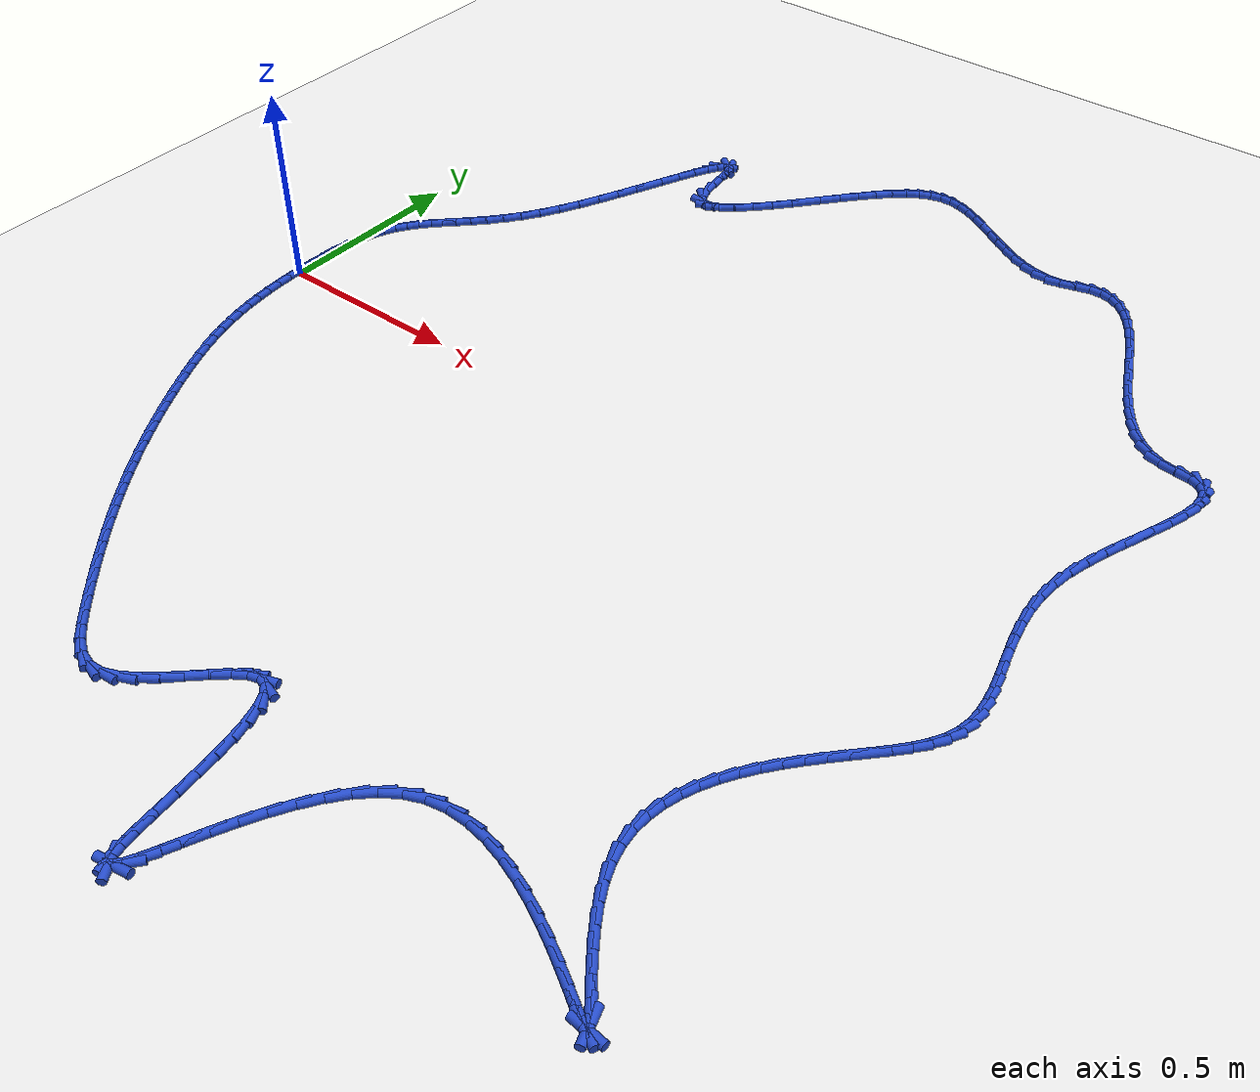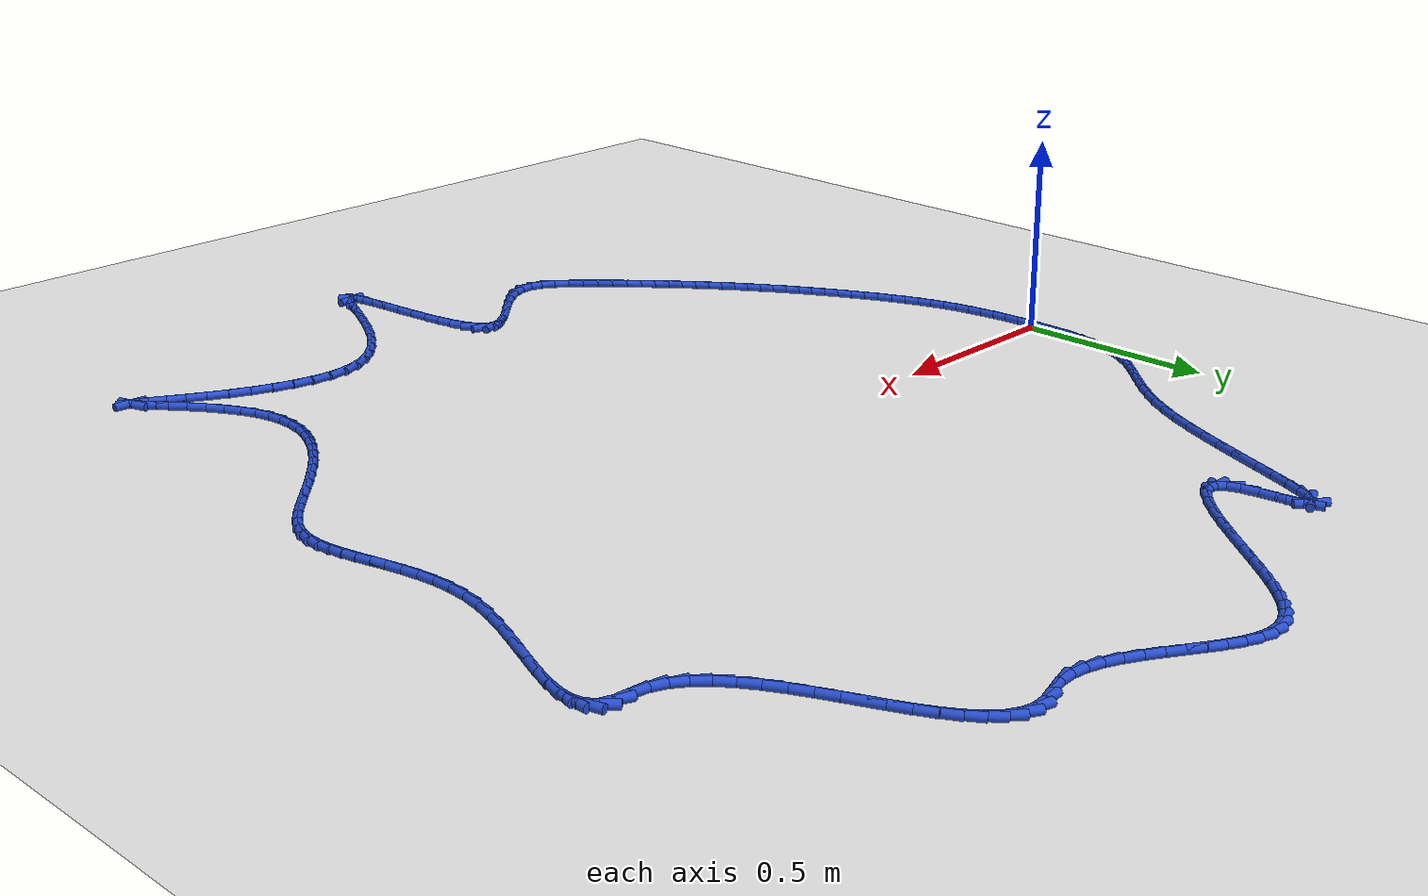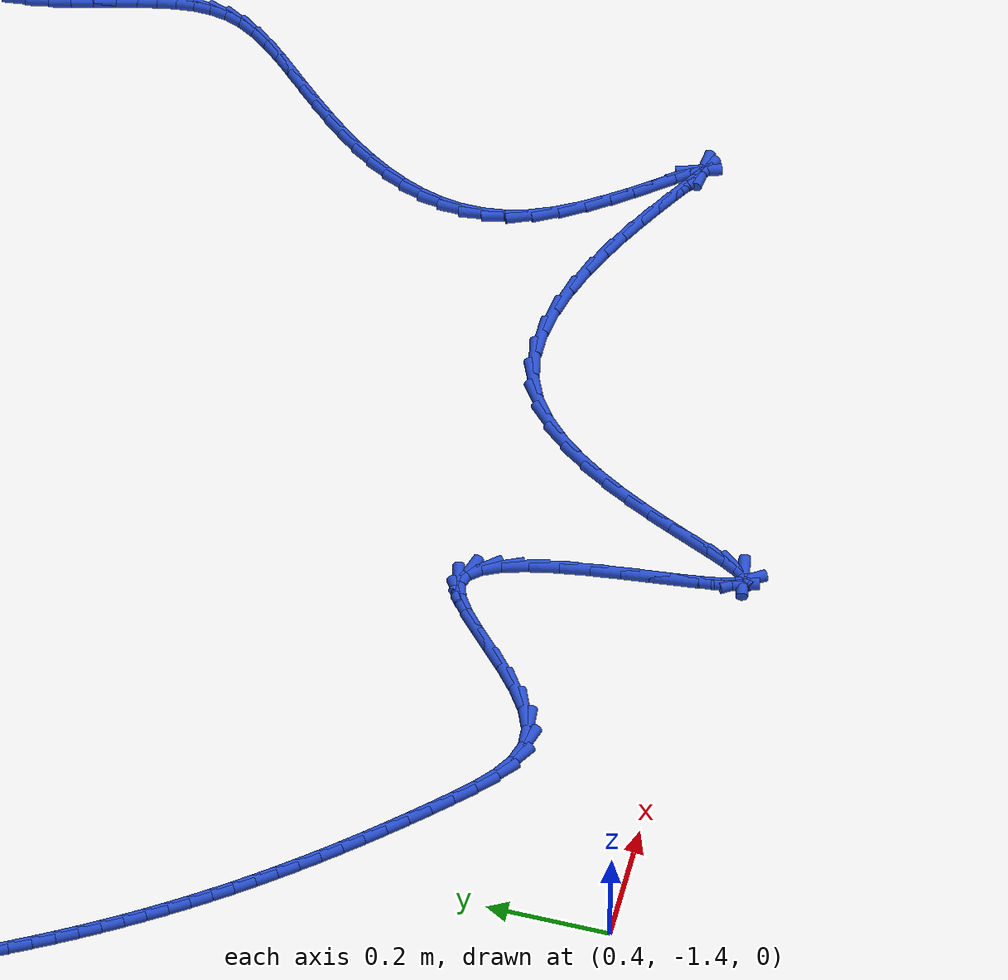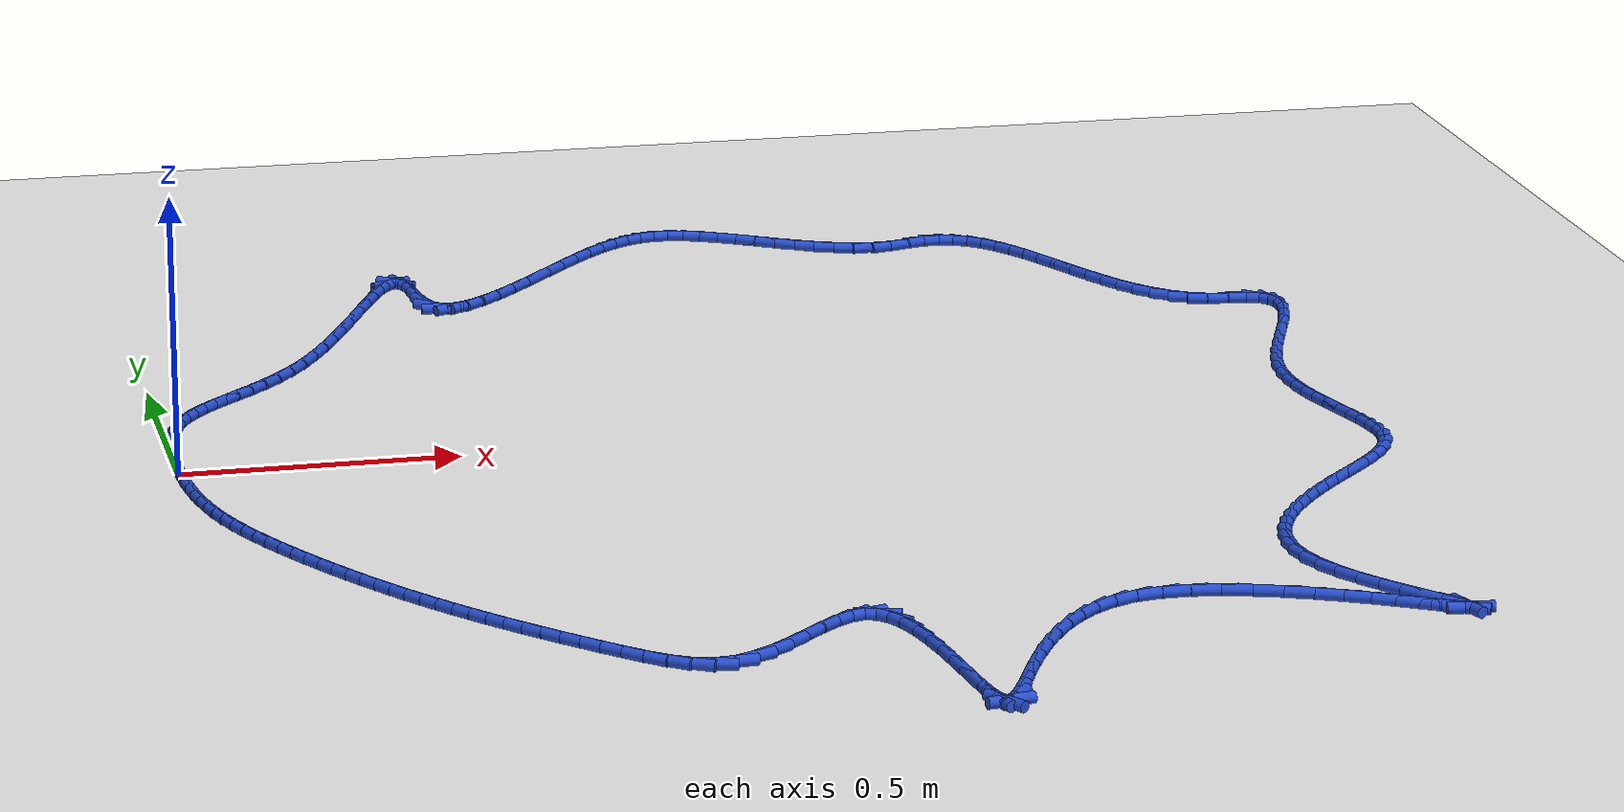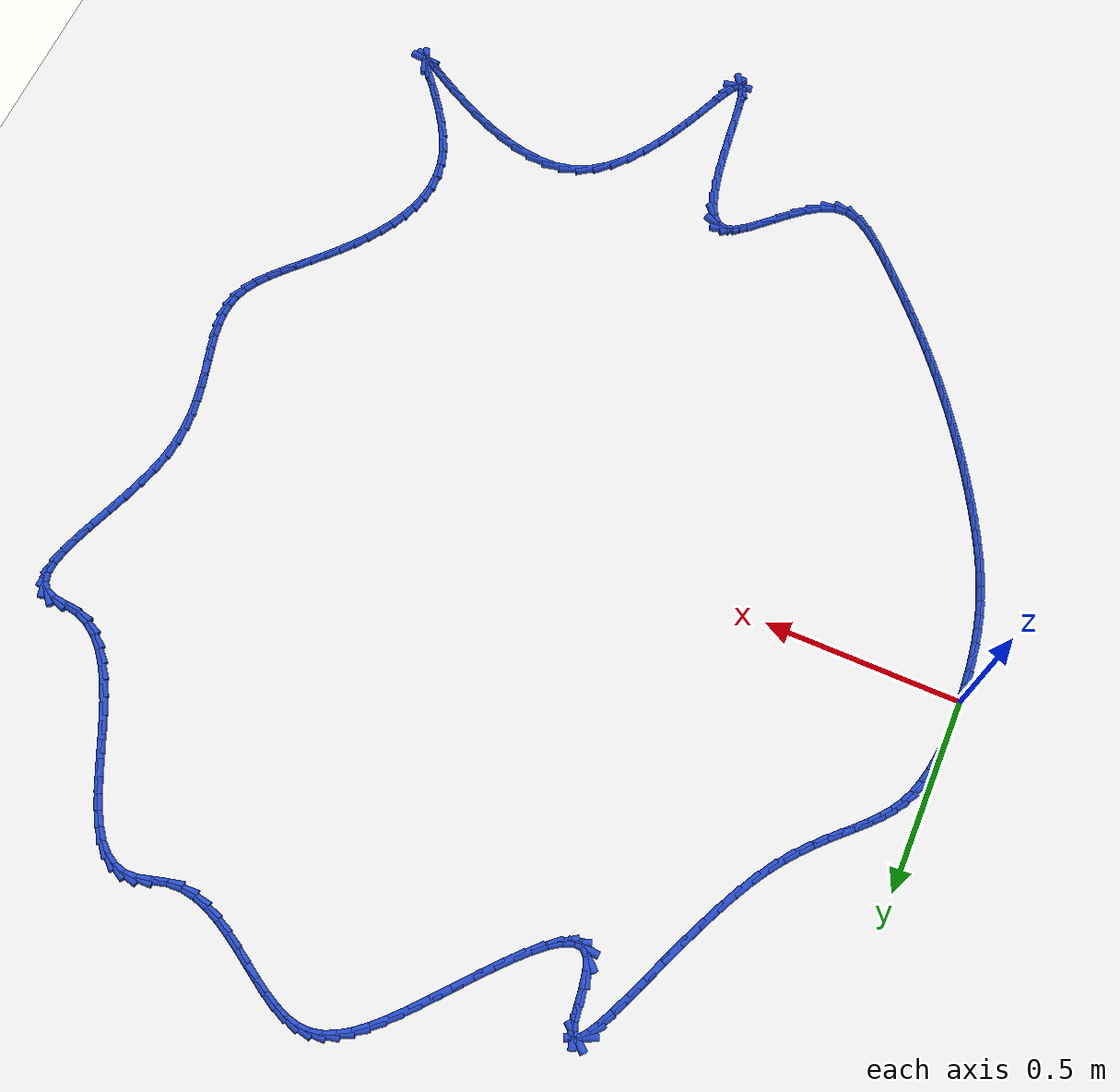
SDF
<sdf version="1.6">
 <world name="default">
  <light name="sun" type="directional">
   <pose>0 0 10 0 -0 0</pose>
   <diffuse>0.8 0.8 0.8 1</diffuse>
   <specular>0.2 0.2 0.2 1</specular>
   <attenuation>
    <range>1000</range>
    <constant>0.9</constant>
    <linear>0.01</linear>
    <quadratic>0.001</quadratic>
   </attenuation>
   <direction>-0.5 0.1 -0.9</direction>
  </light>
  <model name="ground_plane">
   <static>1</static>
   <link name="link">
    <collision name="collision">
     <geometry><plane><normal>0 0 1</normal><size>100 100</size></plane></geometry>
     <surface><friction><ode><mu>100</mu><mu2>50</mu2></ode></friction></surface>
    </collision>
    <visual name="visual">
     <cast_shadows>0</cast_shadows>
     <geometry><plane><normal>0 0 1</normal><size>100 100</size></plane></geometry>
     <material>
      <script><uri>file://media/materials/scripts/gazebo.material</uri><name>Gazebo/WhiteGlow</name></script>
     </material>
    </visual>
   </link>
  </model>
  <gravity>0 0 -9.8</gravity>
  <magnetic_field>6e-06 2.3e-05 -4.2e-05</magnetic_field>
  <atmosphere type="adiabatic"/>
  <physics name="default_physics" default="0" type="ode">
   <max_step_size>0.001</max_step_size>
   <real_time_factor>1</real_time_factor>
   <real_time_update_rate>1000</real_time_update_rate>
  </physics>
  <scene><ambient>0.4 0.4 0.4 1</ambient><background>0.7 0.7 0.7 1</background><shadows>1</shadows></scene>
  <spherical_coordinates>
   <surface_model>EARTH_WGS84</surface_model>
   <latitude_deg>0</latitude_deg>
   <longitude_deg>0</longitude_deg>
   <elevation>0</elevation>
   <heading_deg>0</heading_deg>
  </spherical_coordinates>
  <model name="line">
   <link name="link_0">
    <pose>4.336808689942018e-18 -4.85722573273506e-17 0.01 0 1.57 -1.5625181138658581</pose>
    <collision name="collision">
     <geometry><cylinder><radius>0.01</radius><length>0.08</length></cylinder></geometry>
    </collision>
    <visual name="visual">
     <material>
      <script><name>Gazebo/Blue</name><uri>file://media/materials/scripts/gazebo.material</uri></script>
     </material>
     <geometry><cylinder><radius>0.01</radius><length>0.08</length></cylinder></geometry>
    </visual>
   </link>
   <link name="link_1">
    <pose>-0.00032513500696293993 0.03927509266525714 0.01 0 1.57 1.548888663003254</pose>
    <collision name="collision">
     <geometry><cylinder><radius>0.01</radius><length>0.08</length></cylinder></geometry>
    </collision>
    <visual name="visual">
     <material>
      <script><name>Gazebo/Blue</name><uri>file://media/materials/scripts/gazebo.material</uri></script>
     </material>
     <geometry><cylinder><radius>0.01</radius><length>0.08</length></cylinder></geometry>
    </visual>
   </link>
   <link name="link_2">
    <pose>0.0005396147541233159 0.07874125485230433 0.01 0 1.57 1.5107290629347268</pose>
    <collision name="collision">
     <geometry><cylinder><radius>0.01</radius><length>0.08</length></cylinder></geometry>
    </collision>
    <visual name="visual">
     <material>
      <script><name>Gazebo/Blue</name><uri>file://media/materials/scripts/gazebo.material</uri></script>
     </material>
     <geometry><cylinder><radius>0.01</radius><length>0.08</length></cylinder></geometry>
    </visual>
   </link>
   <link name="link_3">
    <pose>0.0028932114541193013 0.11787680416389244 0.01 0 1.57 1.4630373731802901</pose>
    <collision name="collision">
     <geometry><cylinder><radius>0.01</radius><length>0.08</length></cylinder></geometry>
    </collision>
    <visual name="visual">
     <material>
      <script><name>Gazebo/Blue</name><uri>file://media/materials/scripts/gazebo.material</uri></script>
     </material>
     <geometry><cylinder><radius>0.01</radius><length>0.08</length></cylinder></geometry>
    </visual>
   </link>
   <link name="link_4">
    <pose>0.007034617263885548 0.1561600582027724 0.01 0 1.57 1.4036282458163574</pose>
    <collision name="collision">
     <geometry><cylinder><radius>0.01</radius><length>0.08</length></cylinder></geometry>
    </collision>
    <visual name="visual">
     <material>
      <script><name>Gazebo/Blue</name><uri>file://media/materials/scripts/gazebo.material</uri></script>
     </material>
     <geometry><cylinder><radius>0.01</radius><length>0.08</length></cylinder></geometry>
    </visual>
   </link>
   <link name="link_5">
    <pose>0.013262794354282582 0.19306933457169517 0.01 0 1.57 1.329570792142605</pose>
    <collision name="collision">
     <geometry><cylinder><radius>0.01</radius><length>0.08</length></cylinder></geometry>
    </collision>
    <visual name="visual">
     <material>
      <script><name>Gazebo/Blue</name><uri>file://media/materials/scripts/gazebo.material</uri></script>
     </material>
     <geometry><cylinder><radius>0.01</radius><length>0.08</length></cylinder></geometry>
    </visual>
   </link>
   <link name="link_6">
    <pose>0.02187670489617094 0.22808295087341174 0.01 0 1.57 1.2371334630446404</pose>
    <collision name="collision">
     <geometry><cylinder><radius>0.01</radius><length>0.08</length></cylinder></geometry>
    </collision>
    <visual name="visual">
     <material>
      <script><name>Gazebo/Blue</name><uri>file://media/materials/scripts/gazebo.material</uri></script>
     </material>
     <geometry><cylinder><radius>0.01</radius><length>0.08</length></cylinder></geometry>
    </visual>
   </link>
   <link name="link_7">
    <pose>0.03317531106041114 0.26067922471067284 0.01 0 1.57 1.123995871801635</pose>
    <collision name="collision">
     <geometry><cylinder><radius>0.01</radius><length>0.08</length></cylinder></geometry>
    </collision>
    <visual name="visual">
     <material>
      <script><name>Gazebo/Blue</name><uri>file://media/materials/scripts/gazebo.material</uri></script>
     </material>
     <geometry><cylinder><radius>0.01</radius><length>0.08</length></cylinder></geometry>
    </visual>
   </link>
   <link name="link_8">
    <pose>0.04742049157269053 0.2904115025099059 0.01 0 1.57 1.0099707841121839</pose>
    <collision name="collision">
     <geometry><cylinder><radius>0.01</radius><length>0.08</length></cylinder></geometry>
    </collision>
    <visual name="visual">
     <material>
      <script><name>Gazebo/Blue</name><uri>file://media/materials/scripts/gazebo.material</uri></script>
     </material>
     <geometry><cylinder><radius>0.01</radius><length>0.08</length></cylinder></geometry>
    </visual>
   </link>
   <link name="link_9">
    <pose>0.06449619456429145 0.31759777615582985 0.01 0 1.57 0.9144282323679278</pose>
    <collision name="collision">
     <geometry><cylinder><radius>0.01</radius><length>0.08</length></cylinder></geometry>
    </collision>
    <visual name="visual">
     <material>
      <script><name>Gazebo/Blue</name><uri>file://media/materials/scripts/gazebo.material</uri></script>
     </material>
     <geometry><cylinder><radius>0.01</radius><length>0.08</length></cylinder></geometry>
    </visual>
   </link>
   <link name="link_10">
    <pose>0.08406562135508168 0.34300266199087953 0.01 0 1.57 0.8432323135860406</pose>
    <collision name="collision">
     <geometry><cylinder><radius>0.01</radius><length>0.08</length></cylinder></geometry>
    </collision>
    <visual name="visual">
     <material>
      <script><name>Gazebo/Blue</name><uri>file://media/materials/scripts/gazebo.material</uri></script>
     </material>
     <geometry><cylinder><radius>0.01</radius><length>0.08</length></cylinder></geometry>
    </visual>
   </link>
   <link name="link_11">
    <pose>0.10578920470671183 0.3673963778237334 0.01 0 1.57 0.798284405389385</pose>
    <collision name="collision">
     <geometry><cylinder><radius>0.01</radius><length>0.08</length></cylinder></geometry>
    </collision>
    <visual name="visual">
     <material>
      <script><name>Gazebo/Blue</name><uri>file://media/materials/scripts/gazebo.material</uri></script>
     </material>
     <geometry><cylinder><radius>0.01</radius><length>0.08</length></cylinder></geometry>
    </visual>
   </link>
   <link name="link_12">
    <pose>0.1293273773808324 0.39154914146306974 0.01 0 1.57 0.7787343318453238</pose>
    <collision name="collision">
     <geometry><cylinder><radius>0.01</radius><length>0.08</length></cylinder></geometry>
    </collision>
    <visual name="visual">
     <material>
      <script><name>Gazebo/Blue</name><uri>file://media/materials/scripts/gazebo.material</uri></script>
     </material>
     <geometry><cylinder><radius>0.01</radius><length>0.08</length></cylinder></geometry>
    </visual>
   </link>
   <link name="link_13">
    <pose>0.1543405721390939 0.416231170717567 0.01 0 1.57 0.78219202810619</pose>
    <collision name="collision">
     <geometry><cylinder><radius>0.01</radius><length>0.08</length></cylinder></geometry>
    </collision>
    <visual name="visual">
     <material>
      <script><name>Gazebo/Blue</name><uri>file://media/materials/scripts/gazebo.material</uri></script>
     </material>
     <geometry><cylinder><radius>0.01</radius><length>0.08</length></cylinder></geometry>
    </visual>
   </link>
   <link name="link_14">
    <pose>0.180489221743147 0.44221268339590336 0.01 0 1.57 0.8055183969862442</pose>
    <collision name="collision">
     <geometry><cylinder><radius>0.01</radius><length>0.08</length></cylinder></geometry>
    </collision>
    <visual name="visual">
     <material>
      <script><name>Gazebo/Blue</name><uri>file://media/materials/scripts/gazebo.material</uri></script>
     </material>
     <geometry><cylinder><radius>0.01</radius><length>0.08</length></cylinder></geometry>
    </visual>
   </link>
   <link name="link_15">
    <pose>0.2074337589546421 0.4702638973067574 0.01 0 1.57 0.845202491403653</pose>
    <collision name="collision">
     <geometry><cylinder><radius>0.01</radius><length>0.08</length></cylinder></geometry>
    </collision>
    <visual name="visual">
     <material>
      <script><name>Gazebo/Blue</name><uri>file://media/materials/scripts/gazebo.material</uri></script>
     </material>
     <geometry><cylinder><radius>0.01</radius><length>0.08</length></cylinder></geometry>
    </visual>
   </link>
   <link name="link_16">
    <pose>0.23483461653522988 0.5011550302588071 0.01 0 1.57 0.8975311793298132</pose>
    <collision name="collision">
     <geometry><cylinder><radius>0.01</radius><length>0.08</length></cylinder></geometry>
    </collision>
    <visual name="visual">
     <material>
      <script><name>Gazebo/Blue</name><uri>file://media/materials/scripts/gazebo.material</uri></script>
     </material>
     <geometry><cylinder><radius>0.01</radius><length>0.08</length></cylinder></geometry>
    </visual>
   </link>
   <link name="link_17">
    <pose>0.2623522272465607 0.535656300060731 0.01 0 1.57 0.9587311291340223</pose>
    <collision name="collision">
     <geometry><cylinder><radius>0.01</radius><length>0.08</length></cylinder></geometry>
    </collision>
    <visual name="visual">
     <material>
      <script><name>Gazebo/Blue</name><uri>file://media/materials/scripts/gazebo.material</uri></script>
     </material>
     <geometry><cylinder><radius>0.01</radius><length>0.08</length></cylinder></geometry>
    </visual>
   </link>
   <link name="link_18">
    <pose>0.2896470238502853 0.5745379245212074 0.01 0 1.57 1.0237014605622037</pose>
    <collision name="collision">
     <geometry><cylinder><radius>0.01</radius><length>0.08</length></cylinder></geometry>
    </collision>
    <visual name="visual">
     <material>
      <script><name>Gazebo/Blue</name><uri>file://media/materials/scripts/gazebo.material</uri></script>
     </material>
     <geometry><cylinder><radius>0.01</radius><length>0.08</length></cylinder></geometry>
    </visual>
   </link>
   <link name="link_19">
    <pose>0.31639281145028125 0.618447172197148 0.01 0 1.57 1.076908670592049</pose>
    <collision name="collision">
     <geometry><cylinder><radius>0.01</radius><length>0.08</length></cylinder></geometry>
    </collision>
    <visual name="visual">
     <material>
      <script><name>Gazebo/Blue</name><uri>file://media/materials/scripts/gazebo.material</uri></script>
     </material>
     <geometry><cylinder><radius>0.01</radius><length>0.08</length></cylinder></geometry>
    </visual>
   </link>
   <link name="link_20">
    <pose>0.34240206975986603 0.6667562964551625 0.01 0 1.57 1.1149081977357975</pose>
    <collision name="collision">
     <geometry><cylinder><radius>0.01</radius><length>0.08</length></cylinder></geometry>
    </collision>
    <visual name="visual">
     <material>
      <script><name>Gazebo/Blue</name><uri>file://media/materials/scripts/gazebo.material</uri></script>
     </material>
     <geometry><cylinder><radius>0.01</radius><length>0.08</length></cylinder></geometry>
    </visual>
   </link>
   <link name="link_21">
    <pose>0.36756937375894855 0.7180827426088282 0.01 0 1.57 1.1417892781705619</pose>
    <collision name="collision">
     <geometry><cylinder><radius>0.01</radius><length>0.08</length></cylinder></geometry>
    </collision>
    <visual name="visual">
     <material>
      <script><name>Gazebo/Blue</name><uri>file://media/materials/scripts/gazebo.material</uri></script>
     </material>
     <geometry><cylinder><radius>0.01</radius><length>0.08</length></cylinder></geometry>
    </visual>
   </link>
   <link name="link_22">
    <pose>0.39179037058220784 0.7710340982650828 0.01 0 1.57 1.1599272209017042</pose>
    <collision name="collision">
     <geometry><cylinder><radius>0.01</radius><length>0.08</length></cylinder></geometry>
    </collision>
    <visual name="visual">
     <material>
      <script><name>Gazebo/Blue</name><uri>file://media/materials/scripts/gazebo.material</uri></script>
     </material>
     <geometry><cylinder><radius>0.01</radius><length>0.08</length></cylinder></geometry>
    </visual>
   </link>
   <link name="link_23">
    <pose>0.4149607073643229 0.824217951030863 0.01 0 1.57 1.1704709511569074</pose>
    <collision name="collision">
     <geometry><cylinder><radius>0.01</radius><length>0.08</length></cylinder></geometry>
    </collision>
    <visual name="visual">
     <material>
      <script><name>Gazebo/Blue</name><uri>file://media/materials/scripts/gazebo.material</uri></script>
     </material>
     <geometry><cylinder><radius>0.01</radius><length>0.08</length></cylinder></geometry>
    </visual>
   </link>
   <link name="link_24">
    <pose>0.4369760312399728 0.8762418885131068 0.01 0 1.57 1.1735484409764287</pose>
    <collision name="collision">
     <geometry><cylinder><radius>0.01</radius><length>0.08</length></cylinder></geometry>
    </collision>
    <visual name="visual">
     <material>
      <script><name>Gazebo/Blue</name><uri>file://media/materials/scripts/gazebo.material</uri></script>
     </material>
     <geometry><cylinder><radius>0.01</radius><length>0.08</length></cylinder></geometry>
    </visual>
   </link>
   <link name="link_25">
    <pose>0.45773198934383635 0.9257134983187508 0.01 0 1.57 1.1681200075953615</pose>
    <collision name="collision">
     <geometry><cylinder><radius>0.01</radius><length>0.08</length></cylinder></geometry>
    </collision>
    <visual name="visual">
     <material>
      <script><name>Gazebo/Blue</name><uri>file://media/materials/scripts/gazebo.material</uri></script>
     </material>
     <geometry><cylinder><radius>0.01</radius><length>0.08</length></cylinder></geometry>
    </visual>
   </link>
   <link name="link_26">
    <pose>0.4771242288105931 0.9712403680547333 0.01 0 1.57 1.151283033310312</pose>
    <collision name="collision">
     <geometry><cylinder><radius>0.01</radius><length>0.08</length></cylinder></geometry>
    </collision>
    <visual name="visual">
     <material>
      <script><name>Gazebo/Blue</name><uri>file://media/materials/scripts/gazebo.material</uri></script>
     </material>
     <geometry><cylinder><radius>0.01</radius><length>0.08</length></cylinder></geometry>
    </visual>
   </link>
   <link name="link_27">
    <pose>0.49504839677492163 1.0114300853279914 0.01 0 1.57 1.1162351329151354</pose>
    <collision name="collision">
     <geometry><cylinder><radius>0.01</radius><length>0.08</length></cylinder></geometry>
    </collision>
    <visual name="visual">
     <material>
      <script><name>Gazebo/Blue</name><uri>file://media/materials/scripts/gazebo.material</uri></script>
     </material>
     <geometry><cylinder><radius>0.01</radius><length>0.08</length></cylinder></geometry>
    </visual>
   </link>
   <link name="link_28">
    <pose>0.5114001403715012 1.044890237745462 0.01 0 1.57 1.0458381003610515</pose>
    <collision name="collision">
     <geometry><cylinder><radius>0.01</radius><length>0.08</length></cylinder></geometry>
    </collision>
    <visual name="visual">
     <material>
      <script><name>Gazebo/Blue</name><uri>file://media/materials/scripts/gazebo.material</uri></script>
     </material>
     <geometry><cylinder><radius>0.01</radius><length>0.08</length></cylinder></geometry>
    </visual>
   </link>
   <link name="link_29">
    <pose>0.5260751067350107 1.0702284129140827 0.01 0 1.57 0.8870725300361593</pose>
    <collision name="collision">
     <geometry><cylinder><radius>0.01</radius><length>0.08</length></cylinder></geometry>
    </collision>
    <visual name="visual">
     <material>
      <script><name>Gazebo/Blue</name><uri>file://media/materials/scripts/gazebo.material</uri></script>
     </material>
     <geometry><cylinder><radius>0.01</radius><length>0.08</length></cylinder></geometry>
    </visual>
   </link>
   <link name="link_30">
    <pose>0.5389689430001293 1.0860521984407911 0.01 0 1.57 0.4200723354413961</pose>
    <collision name="collision">
     <geometry><cylinder><radius>0.01</radius><length>0.08</length></cylinder></geometry>
    </collision>
    <visual name="visual">
     <material>
      <script><name>Gazebo/Blue</name><uri>file://media/materials/scripts/gazebo.material</uri></script>
     </material>
     <geometry><cylinder><radius>0.01</radius><length>0.08</length></cylinder></geometry>
    </visual>
   </link>
   <link name="link_31">
    <pose>0.549977296301536 1.0909691819325247 0.01 0 1.57 -0.6859582128199114</pose>
    <collision name="collision">
     <geometry><cylinder><radius>0.01</radius><length>0.08</length></cylinder></geometry>
    </collision>
    <visual name="visual">
     <material>
      <script><name>Gazebo/Blue</name><uri>file://media/materials/scripts/gazebo.material</uri></script>
     </material>
     <geometry><cylinder><radius>0.01</radius><length>0.08</length></cylinder></geometry>
    </visual>
   </link>
   <link name="link_32">
    <pose>0.5589958137739099 1.0835869509962204 0.01 0 1.57 -1.2533304167303803</pose>
    <collision name="collision">
     <geometry><cylinder><radius>0.01</radius><length>0.08</length></cylinder></geometry>
    </collision>
    <visual name="visual">
     <material>
      <script><name>Gazebo/Blue</name><uri>file://media/materials/scripts/gazebo.material</uri></script>
     </material>
     <geometry><cylinder><radius>0.01</radius><length>0.08</length></cylinder></geometry>
    </visual>
   </link>
   <link name="link_33">
    <pose>0.5659201863913298 1.062513283318571 0.01 0 1.57 -1.422246513620611</pose>
    <collision name="collision">
     <geometry><cylinder><radius>0.01</radius><length>0.08</length></cylinder></geometry>
    </collision>
    <visual name="visual">
     <material>
      <script><name>Gazebo/Blue</name><uri>file://media/materials/scripts/gazebo.material</uri></script>
     </material>
     <geometry><cylinder><radius>0.01</radius><length>0.08</length></cylinder></geometry>
    </visual>
   </link>
   <link name="link_34">
    <pose>0.5710616065682401 1.028157496120216 0.01 0 1.57 -1.447030316904505</pose>
    <collision name="collision">
     <geometry><cylinder><radius>0.01</radius><length>0.08</length></cylinder></geometry>
    </collision>
    <visual name="visual">
     <material>
      <script><name>Gazebo/Blue</name><uri>file://media/materials/scripts/gazebo.material</uri></script>
     </material>
     <geometry><cylinder><radius>0.01</radius><length>0.08</length></cylinder></geometry>
    </visual>
   </link>
   <link name="link_35">
    <pose>0.5761640891620258 0.9871413670980163 0.01 0 1.57 -1.3935032936280507</pose>
    <collision name="collision">
     <geometry><cylinder><radius>0.01</radius><length>0.08</length></cylinder></geometry>
    </collision>
    <visual name="visual">
     <material>
      <script><name>Gazebo/Blue</name><uri>file://media/materials/scripts/gazebo.material</uri></script>
     </material>
     <geometry><cylinder><radius>0.01</radius><length>0.08</length></cylinder></geometry>
    </visual>
   </link>
   <link name="link_36">
    <pose>0.5832802741210695 0.947424816849403 0.01 0 1.57 -1.2189861769869361</pose>
    <collision name="collision">
     <geometry><cylinder><radius>0.01</radius><length>0.08</length></cylinder></geometry>
    </collision>
    <visual name="visual">
     <material>
      <script><name>Gazebo/Blue</name><uri>file://media/materials/scripts/gazebo.material</uri></script>
     </material>
     <geometry><cylinder><radius>0.01</radius><length>0.08</length></cylinder></geometry>
    </visual>
   </link>
   <link name="link_37">
    <pose>0.5944617895074628 0.9169642118255512 0.01 0 1.57 -0.7539544601473871</pose>
    <collision name="collision">
     <geometry><cylinder><radius>0.01</radius><length>0.08</length></cylinder></geometry>
    </collision>
    <visual name="visual">
     <material>
      <script><name>Gazebo/Blue</name><uri>file://media/materials/scripts/gazebo.material</uri></script>
     </material>
     <geometry><cylinder><radius>0.01</radius><length>0.08</length></cylinder></geometry>
    </visual>
   </link>
   <link name="link_38">
    <pose>0.6110874085738556 0.9013525853441366 0.01 0 1.57 -0.07490622317966132</pose>
    <collision name="collision">
     <geometry><cylinder><radius>0.01</radius><length>0.08</length></cylinder></geometry>
    </collision>
    <visual name="visual">
     <material>
      <script><name>Gazebo/Blue</name><uri>file://media/materials/scripts/gazebo.material</uri></script>
     </material>
     <geometry><cylinder><radius>0.01</radius><length>0.08</length></cylinder></geometry>
    </visual>
   </link>
   <link name="link_39">
    <pose>0.6326989094805427 0.8997307148915211 0.01 0 1.57 0.3833812059142892</pose>
    <collision name="collision">
     <geometry><cylinder><radius>0.01</radius><length>0.08</length></cylinder></geometry>
    </collision>
    <visual name="visual">
     <material>
      <script><name>Gazebo/Blue</name><uri>file://media/materials/scripts/gazebo.material</uri></script>
     </material>
     <geometry><cylinder><radius>0.01</radius><length>0.08</length></cylinder></geometry>
    </visual>
   </link>
   <link name="link_40">
    <pose>0.6585274524697694 0.9101483645477813 0.01 0 1.57 0.6110287753175572</pose>
    <collision name="collision">
     <geometry><cylinder><radius>0.01</radius><length>0.08</length></cylinder></geometry>
    </collision>
    <visual name="visual">
     <material>
      <script><name>Gazebo/Blue</name><uri>file://media/materials/scripts/gazebo.material</uri></script>
     </material>
     <geometry><cylinder><radius>0.01</radius><length>0.08</length></cylinder></geometry>
    </visual>
   </link>
   <link name="link_41">
    <pose>0.6878041977837813 0.9306552983929937 0.01 0 1.57 0.7308317314494579</pose>
    <collision name="collision">
     <geometry><cylinder><radius>0.01</radius><length>0.08</length></cylinder></geometry>
    </collision>
    <visual name="visual">
     <material>
      <script><name>Gazebo/Blue</name><uri>file://media/materials/scripts/gazebo.material</uri></script>
     </material>
     <geometry><cylinder><radius>0.01</radius><length>0.08</length></cylinder></geometry>
    </visual>
   </link>
   <link name="link_42">
    <pose>0.7197603056648234 0.9593012805072337 0.01 0 1.57 0.7994895696235196</pose>
    <collision name="collision">
     <geometry><cylinder><radius>0.01</radius><length>0.08</length></cylinder></geometry>
    </collision>
    <visual name="visual">
     <material>
      <script><name>Gazebo/Blue</name><uri>file://media/materials/scripts/gazebo.material</uri></script>
     </material>
     <geometry><cylinder><radius>0.01</radius><length>0.08</length></cylinder></geometry>
    </visual>
   </link>
   <link name="link_43">
    <pose>0.753626936355142 0.9941360749705783 0.01 0 1.57 0.840215822517861</pose>
    <collision name="collision">
     <geometry><cylinder><radius>0.01</radius><length>0.08</length></cylinder></geometry>
    </collision>
    <visual name="visual">
     <material>
      <script><name>Gazebo/Blue</name><uri>file://media/materials/scripts/gazebo.material</uri></script>
     </material>
     <geometry><cylinder><radius>0.01</radius><length>0.08</length></cylinder></geometry>
    </visual>
   </link>
   <link name="link_44">
    <pose>0.7886352500969818 1.0332094458631034 0.01 0 1.57 0.8631707522730333</pose>
    <collision name="collision">
     <geometry><cylinder><radius>0.01</radius><length>0.08</length></cylinder></geometry>
    </collision>
    <visual name="visual">
     <material>
      <script><name>Gazebo/Blue</name><uri>file://media/materials/scripts/gazebo.material</uri></script>
     </material>
     <geometry><cylinder><radius>0.01</radius><length>0.08</length></cylinder></geometry>
    </visual>
   </link>
   <link name="link_45">
    <pose>0.8240164071325886 1.0745711572648853 0.01 0 1.57 0.8727369584874677</pose>
    <collision name="collision">
     <geometry><cylinder><radius>0.01</radius><length>0.08</length></cylinder></geometry>
    </collision>
    <visual name="visual">
     <material>
      <script><name>Gazebo/Blue</name><uri>file://media/materials/scripts/gazebo.material</uri></script>
     </material>
     <geometry><cylinder><radius>0.01</radius><length>0.08</length></cylinder></geometry>
    </visual>
   </link>
   <link name="link_46">
    <pose>0.8590015677042075 1.1162709732559999 0.01 0 1.57 0.8700014937404306</pose>
    <collision name="collision">
     <geometry><cylinder><radius>0.01</radius><length>0.08</length></cylinder></geometry>
    </collision>
    <visual name="visual">
     <material>
      <script><name>Gazebo/Blue</name><uri>file://media/materials/scripts/gazebo.material</uri></script>
     </material>
     <geometry><cylinder><radius>0.01</radius><length>0.08</length></cylinder></geometry>
    </visual>
   </link>
   <link name="link_47">
    <pose>0.892826792142787 1.1563649742035496 0.01 0 1.57 0.8538636086401972</pose>
    <collision name="collision">
     <geometry><cylinder><radius>0.01</radius><length>0.08</length></cylinder></geometry>
    </collision>
    <visual name="visual">
     <material>
      <script><name>Gazebo/Blue</name><uri>file://media/materials/scripts/gazebo.material</uri></script>
     </material>
     <geometry><cylinder><radius>0.01</radius><length>0.08</length></cylinder></geometry>
    </visual>
   </link>
   <link name="link_48">
    <pose>0.9251111574946207 1.193402954702385 0.01 0 1.57 0.8219964225265598</pose>
    <collision name="collision">
     <geometry><cylinder><radius>0.01</radius><length>0.08</length></cylinder></geometry>
    </collision>
    <visual name="visual">
     <material>
      <script><name>Gazebo/Blue</name><uri>file://media/materials/scripts/gazebo.material</uri></script>
     </material>
     <geometry><cylinder><radius>0.01</radius><length>0.08</length></cylinder></geometry>
    </visual>
   </link>
   <link name="link_49">
    <pose>0.956125192846392 1.2267744406910595 0.01 0 1.57 0.7701868398920402</pose>
    <collision name="collision">
     <geometry><cylinder><radius>0.01</radius><length>0.08</length></cylinder></geometry>
    </collision>
    <visual name="visual">
     <material>
      <script><name>Gazebo/Blue</name><uri>file://media/materials/scripts/gazebo.material</uri></script>
     </material>
     <geometry><cylinder><radius>0.01</radius><length>0.08</length></cylinder></geometry>
    </visual>
   </link>
   <link name="link_50">
    <pose>0.9862028090315613 1.2559506581199253 0.01 0 1.57 0.6925234191504174</pose>
    <collision name="collision">
     <geometry><cylinder><radius>0.01</radius><length>0.08</length></cylinder></geometry>
    </collision>
    <visual name="visual">
     <material>
      <script><name>Gazebo/Blue</name><uri>file://media/materials/scripts/gazebo.material</uri></script>
     </material>
     <geometry><cylinder><radius>0.01</radius><length>0.08</length></cylinder></geometry>
    </visual>
   </link>
   <link name="link_51">
    <pose>1.0156779168835892 1.2804028329393355 0.01 0 1.57 0.5815358030604832</pose>
    <collision name="collision">
     <geometry><cylinder><radius>0.01</radius><length>0.08</length></cylinder></geometry>
    </collision>
    <visual name="visual">
     <material>
      <script><name>Gazebo/Blue</name><uri>file://media/materials/scripts/gazebo.material</uri></script>
     </material>
     <geometry><cylinder><radius>0.01</radius><length>0.08</length></cylinder></geometry>
    </visual>
   </link>
   <link name="link_52">
    <pose>1.0448844272359366 1.2996021910996431 0.01 0 1.57 0.429805047557264</pose>
    <collision name="collision">
     <geometry><cylinder><radius>0.01</radius><length>0.08</length></cylinder></geometry>
    </collision>
    <visual name="visual">
     <material>
      <script><name>Gazebo/Blue</name><uri>file://media/materials/scripts/gazebo.material</uri></script>
     </material>
     <geometry><cylinder><radius>0.01</radius><length>0.08</length></cylinder></geometry>
    </visual>
   </link>
   <link name="link_53">
    <pose>1.0741562509220632 1.3130199585511995 0.01 0 1.57 0.23510998479612377</pose>
    <collision name="collision">
     <geometry><cylinder><radius>0.01</radius><length>0.08</length></cylinder></geometry>
    </collision>
    <visual name="visual">
     <material>
      <script><name>Gazebo/Blue</name><uri>file://media/materials/scripts/gazebo.material</uri></script>
     </material>
     <geometry><cylinder><radius>0.01</radius><length>0.08</length></cylinder></geometry>
    </visual>
   </link>
   <link name="link_54">
    <pose>1.1038272987754294 1.3201273612443578 0.01 0 1.57 0.00893521651556636</pose>
    <collision name="collision">
     <geometry><cylinder><radius>0.01</radius><length>0.08</length></cylinder></geometry>
    </collision>
    <visual name="visual">
     <material>
      <script><name>Gazebo/Blue</name><uri>file://media/materials/scripts/gazebo.material</uri></script>
     </material>
     <geometry><cylinder><radius>0.01</radius><length>0.08</length></cylinder></geometry>
    </visual>
   </link>
   <link name="link_55">
    <pose>1.134230710025504 1.3203990295365537 0.01 0 1.57 -0.20590039947856606</pose>
    <collision name="collision">
     <geometry><cylinder><radius>0.01</radius><length>0.08</length></cylinder></geometry>
    </collision>
    <visual name="visual">
     <material>
      <script><name>Gazebo/Blue</name><uri>file://media/materials/scripts/gazebo.material</uri></script>
     </material>
     <geometry><cylinder><radius>0.01</radius><length>0.08</length></cylinder></geometry>
    </visual>
   </link>
   <link name="link_56">
    <pose>1.165576664864631 1.3138521034420758 0.01 0 1.57 -0.36217149226945927</pose>
    <collision name="collision">
     <geometry><cylinder><radius>0.01</radius><length>0.08</length></cylinder></geometry>
    </collision>
    <visual name="visual">
     <material>
      <script><name>Gazebo/Blue</name><uri>file://media/materials/scripts/gazebo.material</uri></script>
     </material>
     <geometry><cylinder><radius>0.01</radius><length>0.08</length></cylinder></geometry>
    </visual>
   </link>
   <link name="link_57">
    <pose>1.197818688309911 1.301636115634664 0.01 0 1.57 -0.46519427115432604</pose>
    <collision name="collision">
     <geometry><cylinder><radius>0.01</radius><length>0.08</length></cylinder></geometry>
    </collision>
    <visual name="visual">
     <material>
      <script><name>Gazebo/Blue</name><uri>file://media/materials/scripts/gazebo.material</uri></script>
     </material>
     <geometry><cylinder><radius>0.01</radius><length>0.08</length></cylinder></geometry>
    </visual>
   </link>
   <link name="link_58">
    <pose>1.230878163191035 1.2850424138792378 0.01 0 1.57 -0.5272879270392726</pose>
    <collision name="collision">
     <geometry><cylinder><radius>0.01</radius><length>0.08</length></cylinder></geometry>
    </collision>
    <visual name="visual">
     <material>
      <script><name>Gazebo/Blue</name><uri>file://media/materials/scripts/gazebo.material</uri></script>
     </material>
     <geometry><cylinder><radius>0.01</radius><length>0.08</length></cylinder></geometry>
    </visual>
   </link>
   <link name="link_59">
    <pose>1.2646764723376946 1.2653623459407153 0.01 0 1.57 -0.5573150228196627</pose>
    <collision name="collision">
     <geometry><cylinder><radius>0.01</radius><length>0.08</length></cylinder></geometry>
    </collision>
    <visual name="visual">
     <material>
      <script><name>Gazebo/Blue</name><uri>file://media/materials/scripts/gazebo.material</uri></script>
     </material>
     <geometry><cylinder><radius>0.01</radius><length>0.08</length></cylinder></geometry>
    </visual>
   </link>
   <link name="link_60">
    <pose>1.299134998579582 1.2438872595840178 0.01 0 1.57 -0.5602123364508486</pose>
    <collision name="collision">
     <geometry><cylinder><radius>0.01</radius><length>0.08</length></cylinder></geometry>
    </collision>
    <visual name="visual">
     <material>
      <script><name>Gazebo/Blue</name><uri>file://media/materials/scripts/gazebo.material</uri></script>
     </material>
     <geometry><cylinder><radius>0.01</radius><length>0.08</length></cylinder></geometry>
    </visual>
   </link>
   <link name="link_61">
    <pose>1.3341751247463887 1.221908502574063 0.01 0 1.57 -0.5376264756287165</pose>
    <collision name="collision">
     <geometry><cylinder><radius>0.01</radius><length>0.08</length></cylinder></geometry>
    </collision>
    <visual name="visual">
     <material>
      <script><name>Gazebo/Blue</name><uri>file://media/materials/scripts/gazebo.material</uri></script>
     </material>
     <geometry><cylinder><radius>0.01</radius><length>0.08</length></cylinder></geometry>
    </visual>
   </link>
   <link name="link_62">
    <pose>1.3697182336678062 1.2007174226757715 0.01 0 1.57 -0.4884279258981313</pose>
    <collision name="collision">
     <geometry><cylinder><radius>0.01</radius><length>0.08</length></cylinder></geometry>
    </collision>
    <visual name="visual">
     <material>
      <script><name>Gazebo/Blue</name><uri>file://media/materials/scripts/gazebo.material</uri></script>
     </material>
     <geometry><cylinder><radius>0.01</radius><length>0.08</length></cylinder></geometry>
    </visual>
   </link>
   <link name="link_63">
    <pose>1.4056857081735268 1.181605367654062 0.01 0 1.57 -0.409045825958524</pose>
    <collision name="collision">
     <geometry><cylinder><radius>0.01</radius><length>0.08</length></cylinder></geometry>
    </collision>
    <visual name="visual">
     <material>
      <script><name>Gazebo/Blue</name><uri>file://media/materials/scripts/gazebo.material</uri></script>
     </material>
     <geometry><cylinder><radius>0.01</radius><length>0.08</length></cylinder></geometry>
    </visual>
   </link>
   <link name="link_64">
    <pose>1.4419989310932413 1.1658636852738549 0.01 0 1.57 -0.29410952521227995</pose>
    <collision name="collision">
     <geometry><cylinder><radius>0.01</radius><length>0.08</length></cylinder></geometry>
    </collision>
    <visual name="visual">
     <material>
      <script><name>Gazebo/Blue</name><uri>file://media/materials/scripts/gazebo.material</uri></script>
     </material>
     <geometry><cylinder><radius>0.01</radius><length>0.08</length></cylinder></geometry>
    </visual>
   </link>
   <link name="link_65">
    <pose>1.478579285256642 1.1547837233000688 0.01 0 1.57 -0.13854247090549057</pose>
    <collision name="collision">
     <geometry><cylinder><radius>0.01</radius><length>0.08</length></cylinder></geometry>
    </collision>
    <visual name="visual">
     <material>
      <script><name>Gazebo/Blue</name><uri>file://media/materials/scripts/gazebo.material</uri></script>
     </material>
     <geometry><cylinder><radius>0.01</radius><length>0.08</length></cylinder></geometry>
    </visual>
   </link>
   <link name="link_66">
    <pose>1.5153481534934206 1.1496568294976233 0.01 0 1.57 0.0573554902370289</pose>
    <collision name="collision">
     <geometry><cylinder><radius>0.01</radius><length>0.08</length></cylinder></geometry>
    </collision>
    <visual name="visual">
     <material>
      <script><name>Gazebo/Blue</name><uri>file://media/materials/scripts/gazebo.material</uri></script>
     </material>
     <geometry><cylinder><radius>0.01</radius><length>0.08</length></cylinder></geometry>
    </visual>
   </link>
   <link name="link_67">
    <pose>1.5522269186332682 1.151774351631438 0.01 0 1.57 0.2560856816084314</pose>
    <collision name="collision">
     <geometry><cylinder><radius>0.01</radius><length>0.08</length></cylinder></geometry>
    </collision>
    <visual name="visual">
     <material>
      <script><name>Gazebo/Blue</name><uri>file://media/materials/scripts/gazebo.material</uri></script>
     </material>
     <geometry><cylinder><radius>0.01</radius><length>0.08</length></cylinder></geometry>
    </visual>
   </link>
   <link name="link_68">
    <pose>1.588977768799128 1.161396994147292 0.01 0 1.57 0.27451396121899535</pose>
    <collision name="collision">
     <geometry><cylinder><radius>0.01</radius><length>0.08</length></cylinder></geometry>
    </collision>
    <visual name="visual">
     <material>
      <script><name>Gazebo/Blue</name><uri>file://media/materials/scripts/gazebo.material</uri></script>
     </material>
     <geometry><cylinder><radius>0.01</radius><length>0.08</length></cylinder></geometry>
    </visual>
   </link>
   <link name="link_69">
    <pose>1.6242096336828566 1.1713191313148255 0.01 0 1.57 0.056286231660913164</pose>
    <collision name="collision">
     <geometry><cylinder><radius>0.01</radius><length>0.08</length></cylinder></geometry>
    </collision>
    <visual name="visual">
     <material>
      <script><name>Gazebo/Blue</name><uri>file://media/materials/scripts/gazebo.material</uri></script>
     </material>
     <geometry><cylinder><radius>0.01</radius><length>0.08</length></cylinder></geometry>
    </visual>
   </link>
   <link name="link_70">
    <pose>1.6564383818019035 1.1731350842337112 0.01 0 1.57 -0.2365649904011344</pose>
    <collision name="collision">
     <geometry><cylinder><radius>0.01</radius><length>0.08</length></cylinder></geometry>
    </collision>
    <visual name="visual">
     <material>
      <script><name>Gazebo/Blue</name><uri>file://media/materials/scripts/gazebo.material</uri></script>
     </material>
     <geometry><cylinder><radius>0.01</radius><length>0.08</length></cylinder></geometry>
    </visual>
   </link>
   <link name="link_71">
    <pose>1.6856986495958262 1.1660810473512058 0.01 0 1.57 -0.5103684415493414</pose>
    <collision name="collision">
     <geometry><cylinder><radius>0.01</radius><length>0.08</length></cylinder></geometry>
    </collision>
    <visual name="visual">
     <material>
      <script><name>Gazebo/Blue</name><uri>file://media/materials/scripts/gazebo.material</uri></script>
     </material>
     <geometry><cylinder><radius>0.01</radius><length>0.08</length></cylinder></geometry>
    </visual>
   </link>
   <link name="link_72">
    <pose>1.7123735418426467 1.1511473080356978 0.01 0 1.57 -0.7282313867077387</pose>
    <collision name="collision">
     <geometry><cylinder><radius>0.01</radius><length>0.08</length></cylinder></geometry>
    </collision>
    <visual name="visual">
     <material>
      <script><name>Gazebo/Blue</name><uri>file://media/materials/scripts/gazebo.material</uri></script>
     </material>
     <geometry><cylinder><radius>0.01</radius><length>0.08</length></cylinder></geometry>
    </visual>
   </link>
   <link name="link_73">
    <pose>1.736846163320386 1.129324153655576 0.01 0 1.57 -0.8856810301193223</pose>
    <collision name="collision">
     <geometry><cylinder><radius>0.01</radius><length>0.08</length></cylinder></geometry>
    </collision>
    <visual name="visual">
     <material>
      <script><name>Gazebo/Blue</name><uri>file://media/materials/scripts/gazebo.material</uri></script>
     </material>
     <geometry><cylinder><radius>0.01</radius><length>0.08</length></cylinder></geometry>
    </visual>
   </link>
   <link name="link_74">
    <pose>1.7594996188070655 1.1016018715792273 0.01 0 1.57 -0.9942667689347339</pose>
    <collision name="collision">
     <geometry><cylinder><radius>0.01</radius><length>0.08</length></cylinder></geometry>
    </collision>
    <visual name="visual">
     <material>
      <script><name>Gazebo/Blue</name><uri>file://media/materials/scripts/gazebo.material</uri></script>
     </material>
     <geometry><cylinder><radius>0.01</radius><length>0.08</length></cylinder></geometry>
    </visual>
   </link>
   <link name="link_75">
    <pose>1.7807170130807057 1.0689707491750409 0.01 0 1.57 -1.0666492493274393</pose>
    <collision name="collision">
     <geometry><cylinder><radius>0.01</radius><length>0.08</length></cylinder></geometry>
    </collision>
    <visual name="visual">
     <material>
      <script><name>Gazebo/Blue</name><uri>file://media/materials/scripts/gazebo.material</uri></script>
     </material>
     <geometry><cylinder><radius>0.01</radius><length>0.08</length></cylinder></geometry>
    </visual>
   </link>
   <link name="link_76">
    <pose>1.800881450919329 1.0324210738114052 0.01 0 1.57 -1.1121132912019904</pose>
    <collision name="collision">
     <geometry><cylinder><radius>0.01</radius><length>0.08</length></cylinder></geometry>
    </collision>
    <visual name="visual">
     <material>
      <script><name>Gazebo/Blue</name><uri>file://media/materials/scripts/gazebo.material</uri></script>
     </material>
     <geometry><cylinder><radius>0.01</radius><length>0.08</length></cylinder></geometry>
    </visual>
   </link>
   <link name="link_77">
    <pose>1.8203760371009559 0.9929431328567068 0.01 0 1.57 -1.136542934846392</pose>
    <collision name="collision">
     <geometry><cylinder><radius>0.01</radius><length>0.08</length></cylinder></geometry>
    </collision>
    <visual name="visual">
     <material>
      <script><name>Gazebo/Blue</name><uri>file://media/materials/scripts/gazebo.material</uri></script>
     </material>
     <geometry><cylinder><radius>0.01</radius><length>0.08</length></cylinder></geometry>
    </visual>
   </link>
   <link name="link_78">
    <pose>1.8395838764036077 0.9515272136793356 0.01 0 1.57 -1.143229990157646</pose>
    <collision name="collision">
     <geometry><cylinder><radius>0.01</radius><length>0.08</length></cylinder></geometry>
    </collision>
    <visual name="visual">
     <material>
      <script><name>Gazebo/Blue</name><uri>file://media/materials/scripts/gazebo.material</uri></script>
     </material>
     <geometry><cylinder><radius>0.01</radius><length>0.08</length></cylinder></geometry>
    </visual>
   </link>
   <link name="link_79">
    <pose>1.8588880736053057 0.9091636036476782 0.01 0 1.57 -1.133512496936239</pose>
    <collision name="collision">
     <geometry><cylinder><radius>0.01</radius><length>0.08</length></cylinder></geometry>
    </collision>
    <visual name="visual">
     <material>
      <script><name>Gazebo/Blue</name><uri>file://media/materials/scripts/gazebo.material</uri></script>
     </material>
     <geometry><cylinder><radius>0.01</radius><length>0.08</length></cylinder></geometry>
    </visual>
   </link>
   <link name="link_80">
    <pose>1.8786717334840712 0.8668425901301244 0.01 0 1.57 -1.1071068176928034</pose>
    <collision name="collision">
     <geometry><cylinder><radius>0.01</radius><length>0.08</length></cylinder></geometry>
    </collision>
    <visual name="visual">
     <material>
      <script><name>Gazebo/Blue</name><uri>file://media/materials/scripts/gazebo.material</uri></script>
     </material>
     <geometry><cylinder><radius>0.01</radius><length>0.08</length></cylinder></geometry>
    </visual>
   </link>
   <link name="link_81">
    <pose>1.899317960817926 0.8255544604950612 0.01 0 1.57 -1.0621804570360798</pose>
    <collision name="collision">
     <geometry><cylinder><radius>0.01</radius><length>0.08</length></cylinder></geometry>
    </collision>
    <visual name="visual">
     <material>
      <script><name>Gazebo/Blue</name><uri>file://media/materials/scripts/gazebo.material</uri></script>
     </material>
     <geometry><cylinder><radius>0.01</radius><length>0.08</length></cylinder></geometry>
    </visual>
   </link>
   <link name="link_82">
    <pose>1.9212098603848902 0.7862895021108772 0.01 0 1.57 -0.9952514963757877</pose>
    <collision name="collision">
     <geometry><cylinder><radius>0.01</radius><length>0.08</length></cylinder></geometry>
    </collision>
    <visual name="visual">
     <material>
      <script><name>Gazebo/Blue</name><uri>file://media/materials/scripts/gazebo.material</uri></script>
     </material>
     <geometry><cylinder><radius>0.01</radius><length>0.08</length></cylinder></geometry>
    </visual>
   </link>
   <link name="link_83">
    <pose>1.9447305369629853 0.7500380023459601 0.01 0 1.57 -0.901098544550212</pose>
    <collision name="collision">
     <geometry><cylinder><radius>0.01</radius><length>0.08</length></cylinder></geometry>
    </collision>
    <visual name="visual">
     <material>
      <script><name>Gazebo/Blue</name><uri>file://media/materials/scripts/gazebo.material</uri></script>
     </material>
     <geometry><cylinder><radius>0.01</radius><length>0.08</length></cylinder></geometry>
    </visual>
   </link>
   <link name="link_84">
    <pose>1.9702630953302323 0.7177902485686987 0.01 0 1.57 -0.7731876600633841</pose>
    <collision name="collision">
     <geometry><cylinder><radius>0.01</radius><length>0.08</length></cylinder></geometry>
    </collision>
    <visual name="visual">
     <material>
      <script><name>Gazebo/Blue</name><uri>file://media/materials/scripts/gazebo.material</uri></script>
     </material>
     <geometry><cylinder><radius>0.01</radius><length>0.08</length></cylinder></geometry>
    </visual>
   </link>
   <link name="link_85">
    <pose>1.9981906402646539 0.6905365281474807 0.01 0 1.57 -0.6058011317473849</pose>
    <collision name="collision">
     <geometry><cylinder><radius>0.01</radius><length>0.08</length></cylinder></geometry>
    </collision>
    <visual name="visual">
     <material>
      <script><name>Gazebo/Blue</name><uri>file://media/materials/scripts/gazebo.material</uri></script>
     </material>
     <geometry><cylinder><radius>0.01</radius><length>0.08</length></cylinder></geometry>
    </visual>
   </link>
   <link name="link_86">
    <pose>2.0288962765442697 0.6692671284506948 0.01 0 1.57 -0.39940177573918967</pose>
    <collision name="collision">
     <geometry><cylinder><radius>0.01</radius><length>0.08</length></cylinder></geometry>
    </collision>
    <visual name="visual">
     <material>
      <script><name>Gazebo/Blue</name><uri>file://media/materials/scripts/gazebo.material</uri></script>
     </material>
     <geometry><cylinder><radius>0.01</radius><length>0.08</length></cylinder></geometry>
    </visual>
   </link>
   <link name="link_87">
    <pose>2.0627631089471015 0.6549723368467284 0.01 0 1.57 -0.17007441226633815</pose>
    <collision name="collision">
     <geometry><cylinder><radius>0.01</radius><length>0.08</length></cylinder></geometry>
    </collision>
    <visual name="visual">
     <material>
      <script><name>Gazebo/Blue</name><uri>file://media/materials/scripts/gazebo.material</uri></script>
     </material>
     <geometry><cylinder><radius>0.01</radius><length>0.08</length></cylinder></geometry>
    </visual>
   </link>
   <link name="link_88">
    <pose>2.100101372638777 0.6485601088254555 0.01 0 1.57 -0.08676398623313394</pose>
    <collision name="collision">
     <geometry><cylinder><radius>0.01</radius><length>0.08</length></cylinder></geometry>
    </collision>
    <visual name="visual">
     <material>
      <script><name>Gazebo/Blue</name><uri>file://media/materials/scripts/gazebo.material</uri></script>
     </material>
     <geometry><cylinder><radius>0.01</radius><length>0.08</length></cylinder></geometry>
    </visual>
   </link>
   <link name="link_89">
    <pose>2.136327761023231 0.6454090519504484 0.01 0 1.57 -0.36391834789815797</pose>
    <collision name="collision">
     <geometry><cylinder><radius>0.01</radius><length>0.08</length></cylinder></geometry>
    </collision>
    <visual name="visual">
     <material>
      <script><name>Gazebo/Blue</name><uri>file://media/materials/scripts/gazebo.material</uri></script>
     </material>
     <geometry><cylinder><radius>0.01</radius><length>0.08</length></cylinder></geometry>
    </visual>
   </link>
   <link name="link_90">
    <pose>2.162348594249542 0.635498159497639 0.01 0 1.57 -0.8463129193081445</pose>
    <collision name="collision">
     <geometry><cylinder><radius>0.01</radius><length>0.08</length></cylinder></geometry>
    </collision>
    <visual name="visual">
     <material>
      <script><name>Gazebo/Blue</name><uri>file://media/materials/scripts/gazebo.material</uri></script>
     </material>
     <geometry><cylinder><radius>0.01</radius><length>0.08</length></cylinder></geometry>
    </visual>
   </link>
   <link name="link_91">
    <pose>2.1778983416320465 0.617928449398913 0.01 0 1.57 -1.3113086702979015</pose>
    <collision name="collision">
     <geometry><cylinder><radius>0.01</radius><length>0.08</length></cylinder></geometry>
    </collision>
    <visual name="visual">
     <material>
      <script><name>Gazebo/Blue</name><uri>file://media/materials/scripts/gazebo.material</uri></script>
     </material>
     <geometry><cylinder><radius>0.01</radius><length>0.08</length></cylinder></geometry>
    </visual>
   </link>
   <link name="link_92">
    <pose>2.184374965463743 0.5935319064398422 0.01 0 1.57 1.5313800111826732</pose>
    <collision name="collision">
     <geometry><cylinder><radius>0.01</radius><length>0.08</length></cylinder></geometry>
    </collision>
    <visual name="visual">
     <material>
      <script><name>Gazebo/Blue</name><uri>file://media/materials/scripts/gazebo.material</uri></script>
     </material>
     <geometry><cylinder><radius>0.01</radius><length>0.08</length></cylinder></geometry>
    </visual>
   </link>
   <link name="link_93">
    <pose>2.1831764280376253 0.563140515405999 0.01 0 1.57 1.3635524640347216</pose>
    <collision name="collision">
     <geometry><cylinder><radius>0.01</radius><length>0.08</length></cylinder></geometry>
    </collision>
    <visual name="visual">
     <material>
      <script><name>Gazebo/Blue</name><uri>file://media/materials/scripts/gazebo.material</uri></script>
     </material>
     <geometry><cylinder><radius>0.01</radius><length>0.08</length></cylinder></geometry>
    </visual>
   </link>
   <link name="link_94">
    <pose>2.17570069164669 0.5275862610829544 0.01 0 1.57 1.270406099410097</pose>
    <collision name="collision">
     <geometry><cylinder><radius>0.01</radius><length>0.08</length></cylinder></geometry>
    </collision>
    <visual name="visual">
     <material>
      <script><name>Gazebo/Blue</name><uri>file://media/materials/scripts/gazebo.material</uri></script>
     </material>
     <geometry><cylinder><radius>0.01</radius><length>0.08</length></cylinder></geometry>
    </visual>
   </link>
   <link name="link_95">
    <pose>2.1633457185839338 0.4877011282562819 0.01 0 1.57 1.2207995499956517</pose>
    <collision name="collision">
     <geometry><cylinder><radius>0.01</radius><length>0.08</length></cylinder></geometry>
    </collision>
    <visual name="visual">
     <material>
      <script><name>Gazebo/Blue</name><uri>file://media/materials/scripts/gazebo.material</uri></script>
     </material>
     <geometry><cylinder><radius>0.01</radius><length>0.08</length></cylinder></geometry>
    </visual>
   </link>
   <link name="link_96">
    <pose>2.147509471142352 0.44431710171155203 0.01 0 1.57 1.1997001630612982</pose>
    <collision name="collision">
     <geometry><cylinder><radius>0.01</radius><length>0.08</length></cylinder></geometry>
    </collision>
    <visual name="visual">
     <material>
      <script><name>Gazebo/Blue</name><uri>file://media/materials/scripts/gazebo.material</uri></script>
     </material>
     <geometry><cylinder><radius>0.01</radius><length>0.08</length></cylinder></geometry>
    </visual>
   </link>
   <link name="link_97">
    <pose>2.1295899116149415 0.3982661662343381 0.01 0 1.57 1.200220151817474</pose>
    <collision name="collision">
     <geometry><cylinder><radius>0.01</radius><length>0.08</length></cylinder></geometry>
    </collision>
    <visual name="visual">
     <material>
      <script><name>Gazebo/Blue</name><uri>file://media/materials/scripts/gazebo.material</uri></script>
     </material>
     <geometry><cylinder><radius>0.01</radius><length>0.08</length></cylinder></geometry>
    </visual>
   </link>
   <link name="link_98">
    <pose>2.1109850022946977 0.35038030661021136 0.01 0 1.57 1.2199574219983988</pose>
    <collision name="collision">
     <geometry><cylinder><radius>0.01</radius><length>0.08</length></cylinder></geometry>
    </collision>
    <visual name="visual">
     <material>
      <script><name>Gazebo/Blue</name><uri>file://media/materials/scripts/gazebo.material</uri></script>
     </material>
     <geometry><cylinder><radius>0.01</radius><length>0.08</length></cylinder></geometry>
    </visual>
   </link>
   <link name="link_99">
    <pose>2.093092705474617 0.30149150762474336 0.01 0 1.57 1.2595668442967862</pose>
    <collision name="collision">
     <geometry><cylinder><radius>0.01</radius><length>0.08</length></cylinder></geometry>
    </collision>
    <visual name="visual">
     <material>
      <script><name>Gazebo/Blue</name><uri>file://media/materials/scripts/gazebo.material</uri></script>
     </material>
     <geometry><cylinder><radius>0.01</radius><length>0.08</length></cylinder></geometry>
    </visual>
   </link>
   <link name="link_100">
    <pose>2.0773109834476955 0.2524317540635074 0.01 0 1.57 1.3224465058464312</pose>
    <collision name="collision">
     <geometry><cylinder><radius>0.01</radius><length>0.08</length></cylinder></geometry>
    </collision>
    <visual name="visual">
     <material>
      <script><name>Gazebo/Blue</name><uri>file://media/materials/scripts/gazebo.material</uri></script>
     </material>
     <geometry><cylinder><radius>0.01</radius><length>0.08</length></cylinder></geometry>
    </visual>
   </link>
   <link name="link_101">
    <pose>2.0650377985069284 0.20403303071207396 0.01 0 1.57 1.413974672898532</pose>
    <collision name="collision">
     <geometry><cylinder><radius>0.01</radius><length>0.08</length></cylinder></geometry>
    </collision>
    <visual name="visual">
     <material>
      <script><name>Gazebo/Blue</name><uri>file://media/materials/scripts/gazebo.material</uri></script>
     </material>
     <geometry><cylinder><radius>0.01</radius><length>0.08</length></cylinder></geometry>
    </visual>
   </link>
   <link name="link_102">
    <pose>2.057617683832936 0.15710592068556725 0.01 0 1.57 1.5186898717853423</pose>
    <collision name="collision">
     <geometry><cylinder><radius>0.01</radius><length>0.08</length></cylinder></geometry>
    </collision>
    <visual name="visual">
     <material>
      <script><name>Gazebo/Blue</name><uri>file://media/materials/scripts/gazebo.material</uri></script>
     </material>
     <geometry><cylinder><radius>0.01</radius><length>0.08</length></cylinder></geometry>
    </visual>
   </link>
   <link name="link_103">
    <pose>2.0552656922893964 0.11200858023953986 0.01 0 1.57 -1.5280380355078849</pose>
    <collision name="collision">
     <geometry><cylinder><radius>0.01</radius><length>0.08</length></cylinder></geometry>
    </collision>
    <visual name="visual">
     <material>
      <script><name>Gazebo/Blue</name><uri>file://media/materials/scripts/gazebo.material</uri></script>
     </material>
     <geometry><cylinder><radius>0.01</radius><length>0.08</length></cylinder></geometry>
    </visual>
   </link>
   <link name="link_104">
    <pose>2.0571199997787764 0.06866780967372066 0.01 0 1.57 -1.4477041576035494</pose>
    <collision name="collision">
     <geometry><cylinder><radius>0.01</radius><length>0.08</length></cylinder></geometry>
    </collision>
    <visual name="visual">
     <material>
      <script><name>Gazebo/Blue</name><uri>file://media/materials/scripts/gazebo.material</uri></script>
     </material>
     <geometry><cylinder><radius>0.01</radius><length>0.08</length></cylinder></geometry>
    </visual>
   </link>
   <link name="link_105">
    <pose>2.0622758812644957 0.026993224803223494 0.01 0 1.57 -1.3846243704549204</pose>
    <collision name="collision">
     <geometry><cylinder><radius>0.01</radius><length>0.08</length></cylinder></geometry>
    </collision>
    <visual name="visual">
     <material>
      <script><name>Gazebo/Blue</name><uri>file://media/materials/scripts/gazebo.material</uri></script>
     </material>
     <geometry><cylinder><radius>0.01</radius><length>0.08</length></cylinder></geometry>
    </visual>
   </link>
   <link name="link_106">
    <pose>2.069828611709974 -0.013105558556835623 0.01 0 1.57 -1.3407032527517386</pose>
    <collision name="collision">
     <geometry><cylinder><radius>0.01</radius><length>0.08</length></cylinder></geometry>
    </collision>
    <visual name="visual">
     <material>
      <script><name>Gazebo/Blue</name><uri>file://media/materials/scripts/gazebo.material</uri></script>
     </material>
     <geometry><cylinder><radius>0.01</radius><length>0.08</length></cylinder></geometry>
    </visual>
   </link>
   <link name="link_107">
    <pose>2.07887346607863 -0.05171892459134222 0.01 0 1.57 -1.3175488682389356</pose>
    <collision name="collision">
     <geometry><cylinder><radius>0.01</radius><length>0.08</length></cylinder></geometry>
    </collision>
    <visual name="visual">
     <material>
      <script><name>Gazebo/Blue</name><uri>file://media/materials/scripts/gazebo.material</uri></script>
     </material>
     <geometry><cylinder><radius>0.01</radius><length>0.08</length></cylinder></geometry>
    </visual>
   </link>
   <link name="link_108">
    <pose>2.0885057193338827 -0.0889372574851818 0.01 0 1.57 -1.31701860037854</pose>
    <collision name="collision">
     <geometry><cylinder><radius>0.01</radius><length>0.08</length></cylinder></geometry>
    </collision>
    <visual name="visual">
     <material>
      <script><name>Gazebo/Blue</name><uri>file://media/materials/scripts/gazebo.material</uri></script>
     </material>
     <geometry><cylinder><radius>0.01</radius><length>0.08</length></cylinder></geometry>
    </visual>
   </link>
   <link name="link_109">
    <pose>2.097820646439151 -0.12485094142323844 0.01 0 1.57 -1.341664296343314</pose>
    <collision name="collision">
     <geometry><cylinder><radius>0.01</radius><length>0.08</length></cylinder></geometry>
    </collision>
    <visual name="visual">
     <material>
      <script><name>Gazebo/Blue</name><uri>file://media/materials/scripts/gazebo.material</uri></script>
     </material>
     <geometry><cylinder><radius>0.01</radius><length>0.08</length></cylinder></geometry>
    </visual>
   </link>
   <link name="link_110">
    <pose>2.105913522357855 -0.1595503605903981 0.01 0 1.57 -1.3949399940498004</pose>
    <collision name="collision">
     <geometry><cylinder><radius>0.01</radius><length>0.08</length></cylinder></geometry>
    </collision>
    <visual name="visual">
     <material>
      <script><name>Gazebo/Blue</name><uri>file://media/materials/scripts/gazebo.material</uri></script>
     </material>
     <geometry><cylinder><radius>0.01</radius><length>0.08</length></cylinder></geometry>
    </visual>
   </link>
   <link name="link_111">
    <pose>2.111879622053412 -0.19312589917154493 0.01 0 1.57 -1.4808609102739394</pose>
    <collision name="collision">
     <geometry><cylinder><radius>0.01</radius><length>0.08</length></cylinder></geometry>
    </collision>
    <visual name="visual">
     <material>
      <script><name>Gazebo/Blue</name><uri>file://media/materials/scripts/gazebo.material</uri></script>
     </material>
     <geometry><cylinder><radius>0.01</radius><length>0.08</length></cylinder></geometry>
    </visual>
   </link>
   <link name="link_112">
    <pose>2.1148142204892424 -0.2256679413515648 0.01 0 1.57 1.539108779333159</pose>
    <collision name="collision">
     <geometry><cylinder><radius>0.01</radius><length>0.08</length></cylinder></geometry>
    </collision>
    <visual name="visual">
     <material>
      <script><name>Gazebo/Blue</name><uri>file://media/materials/scripts/gazebo.material</uri></script>
     </material>
     <geometry><cylinder><radius>0.01</radius><length>0.08</length></cylinder></geometry>
    </visual>
   </link>
   <link name="link_113">
    <pose>2.113812592628765 -0.2572668713153419 0.01 0 1.57 1.383009241567512</pose>
    <collision name="collision">
     <geometry><cylinder><radius>0.01</radius><length>0.08</length></cylinder></geometry>
    </collision>
    <visual name="visual">
     <material>
      <script><name>Gazebo/Blue</name><uri>file://media/materials/scripts/gazebo.material</uri></script>
     </material>
     <geometry><cylinder><radius>0.01</radius><length>0.08</length></cylinder></geometry>
    </visual>
   </link>
   <link name="link_114">
    <pose>2.1079700134353985 -0.28801307324776204 0.01 0 1.57 1.2030797857507047</pose>
    <collision name="collision">
     <geometry><cylinder><radius>0.01</radius><length>0.08</length></cylinder></geometry>
    </collision>
    <visual name="visual">
     <material>
      <script><name>Gazebo/Blue</name><uri>file://media/materials/scripts/gazebo.material</uri></script>
     </material>
     <geometry><cylinder><radius>0.01</radius><length>0.08</length></cylinder></geometry>
    </visual>
   </link>
   <link name="link_115">
    <pose>2.0964179944298627 -0.3179997409419714 0.01 0 1.57 1.0417502753152044</pose>
    <collision name="collision">
     <geometry><cylinder><radius>0.01</radius><length>0.08</length></cylinder></geometry>
    </collision>
    <visual name="visual">
     <material>
      <script><name>Gazebo/Blue</name><uri>file://media/materials/scripts/gazebo.material</uri></script>
     </material>
     <geometry><cylinder><radius>0.01</radius><length>0.08</length></cylinder></geometry>
    </visual>
   </link>
   <link name="link_116">
    <pose>2.0792334137213793 -0.3473933673667404 0.01 0 1.57 0.9285296731130407</pose>
    <collision name="collision">
     <geometry><cylinder><radius>0.01</radius><length>0.08</length></cylinder></geometry>
    </collision>
    <visual name="visual">
     <material>
      <script><name>Gazebo/Blue</name><uri>file://media/materials/scripts/gazebo.material</uri></script>
     </material>
     <geometry><cylinder><radius>0.01</radius><length>0.08</length></cylinder></geometry>
    </visual>
   </link>
   <link name="link_117">
    <pose>2.057505223901524 -0.3764389168755155 0.01 0 1.57 0.8557895625418201</pose>
    <collision name="collision">
     <geometry><cylinder><radius>0.01</radius><length>0.08</length></cylinder></geometry>
    </collision>
    <visual name="visual">
     <material>
      <script><name>Gazebo/Blue</name><uri>file://media/materials/scripts/gazebo.material</uri></script>
     </material>
     <geometry><cylinder><radius>0.01</radius><length>0.08</length></cylinder></geometry>
    </visual>
   </link>
   <link name="link_118">
    <pose>2.032371975145218 -0.4053851993796614 0.01 0 1.57 0.8154103969055485</pose>
    <collision name="collision">
     <geometry><cylinder><radius>0.01</radius><length>0.08</length></cylinder></geometry>
    </collision>
    <visual name="visual">
     <material>
      <script><name>Gazebo/Blue</name><uri>file://media/materials/scripts/gazebo.material</uri></script>
     </material>
     <geometry><cylinder><radius>0.01</radius><length>0.08</length></cylinder></geometry>
    </visual>
   </link>
   <link name="link_119">
    <pose>2.004972217627379 -0.43448102479054446 0.01 0 1.57 0.8020534754764346</pose>
    <collision name="collision">
     <geometry><cylinder><radius>0.01</radius><length>0.08</length></cylinder></geometry>
    </collision>
    <visual name="visual">
     <material>
      <script><name>Gazebo/Blue</name><uri>file://media/materials/scripts/gazebo.material</uri></script>
     </material>
     <geometry><cylinder><radius>0.01</radius><length>0.08</length></cylinder></geometry>
    </visual>
   </link>
   <link name="link_120">
    <pose>1.9764445015229273 -0.4639752030195309 0.01 0 1.57 0.8113382721984551</pose>
    <collision name="collision">
     <geometry><cylinder><radius>0.01</radius><length>0.08</length></cylinder></geometry>
    </collision>
    <visual name="visual">
     <material>
      <script><name>Gazebo/Blue</name><uri>file://media/materials/scripts/gazebo.material</uri></script>
     </material>
     <geometry><cylinder><radius>0.01</radius><length>0.08</length></cylinder></geometry>
    </visual>
   </link>
   <link name="link_121">
    <pose>1.9478529491179377 -0.49408994474274004 0.01 0 1.57 0.8328014312405166</pose>
    <collision name="collision">
     <geometry><cylinder><radius>0.01</radius><length>0.08</length></cylinder></geometry>
    </collision>
    <visual name="visual">
     <material>
      <script><name>Gazebo/Blue</name><uri>file://media/materials/scripts/gazebo.material</uri></script>
     </material>
     <geometry><cylinder><radius>0.01</radius><length>0.08</length></cylinder></geometry>
    </visual>
   </link>
   <link name="link_122">
    <pose>1.9198374598576915 -0.5248958507584004 0.01 0 1.57 0.8633130704508035</pose>
    <collision name="collision">
     <geometry><cylinder><radius>0.01</radius><length>0.08</length></cylinder></geometry>
    </collision>
    <visual name="visual">
     <material>
      <script><name>Gazebo/Blue</name><uri>file://media/materials/scripts/gazebo.material</uri></script>
     </material>
     <geometry><cylinder><radius>0.01</radius><length>0.08</length></cylinder></geometry>
    </visual>
   </link>
   <link name="link_123">
    <pose>1.8928878538863017 -0.5564098861281953 0.01 0 1.57 0.9036127127639266</pose>
    <collision name="collision">
     <geometry><cylinder><radius>0.01</radius><length>0.08</length></cylinder></geometry>
    </collision>
    <visual name="visual">
     <material>
      <script><name>Gazebo/Blue</name><uri>file://media/materials/scripts/gazebo.material</uri></script>
     </material>
     <geometry><cylinder><radius>0.01</radius><length>0.08</length></cylinder></geometry>
    </visual>
   </link>
   <link name="link_124">
    <pose>1.867493777603774 -0.5886489538206836 0.01 0 1.57 0.9547547132159241</pose>
    <collision name="collision">
     <geometry><cylinder><radius>0.01</radius><length>0.08</length></cylinder></geometry>
    </collision>
    <visual name="visual">
     <material>
      <script><name>Gazebo/Blue</name><uri>file://media/materials/scripts/gazebo.material</uri></script>
     </material>
     <geometry><cylinder><radius>0.01</radius><length>0.08</length></cylinder></geometry>
    </visual>
   </link>
   <link name="link_125">
    <pose>1.844144877410118 -0.6216299568044242 0.01 0 1.57 1.0180435977746203</pose>
    <collision name="collision">
     <geometry><cylinder><radius>0.01</radius><length>0.08</length></cylinder></geometry>
    </collision>
    <visual name="visual">
     <material>
      <script><name>Gazebo/Blue</name><uri>file://media/materials/scripts/gazebo.material</uri></script>
     </material>
     <geometry><cylinder><radius>0.01</radius><length>0.08</length></cylinder></geometry>
    </visual>
   </link>
   <link name="link_126">
    <pose>1.8233307997053398 -0.6553697980479763 0.01 0 1.57 1.0948984013478125</pose>
    <collision name="collision">
     <geometry><cylinder><radius>0.01</radius><length>0.08</length></cylinder></geometry>
    </collision>
    <visual name="visual">
     <material>
      <script><name>Gazebo/Blue</name><uri>file://media/materials/scripts/gazebo.material</uri></script>
     </material>
     <geometry><cylinder><radius>0.01</radius><length>0.08</length></cylinder></geometry>
    </visual>
   </link>
   <link name="link_127">
    <pose>1.805541190889447 -0.6898853805198965 0.01 0 1.57 1.1865793692703386</pose>
    <collision name="collision">
     <geometry><cylinder><radius>0.01</radius><length>0.08</length></cylinder></geometry>
    </collision>
    <visual name="visual">
     <material>
      <script><name>Gazebo/Blue</name><uri>file://media/materials/scripts/gazebo.material</uri></script>
     </material>
     <geometry><cylinder><radius>0.01</radius><length>0.08</length></cylinder></geometry>
    </visual>
   </link>
   <link name="link_128">
    <pose>1.791265697362448 -0.7251936071887444 0.01 0 1.57 1.2937163598619312</pose>
    <collision name="collision">
     <geometry><cylinder><radius>0.01</radius><length>0.08</length></cylinder></geometry>
    </collision>
    <visual name="visual">
     <material>
      <script><name>Gazebo/Blue</name><uri>file://media/materials/scripts/gazebo.material</uri></script>
     </material>
     <geometry><cylinder><radius>0.01</radius><length>0.08</length></cylinder></geometry>
    </visual>
   </link>
   <link name="link_129">
    <pose>1.7809939655243503 -0.7613113810230785 0.01 0 1.57 1.4156466337580609</pose>
    <collision name="collision">
     <geometry><cylinder><radius>0.01</radius><length>0.08</length></cylinder></geometry>
    </collision>
    <visual name="visual">
     <material>
      <script><name>Gazebo/Blue</name><uri>file://media/materials/scripts/gazebo.material</uri></script>
     </material>
     <geometry><cylinder><radius>0.01</radius><length>0.08</length></cylinder></geometry>
    </visual>
   </link>
   <link name="link_130">
    <pose>1.7752156417751612 -0.7982556049914572 0.01 0 1.57 1.5497536472109306</pose>
    <collision name="collision">
     <geometry><cylinder><radius>0.01</radius><length>0.08</length></cylinder></geometry>
    </collision>
    <visual name="visual">
     <material>
      <script><name>Gazebo/Blue</name><uri>file://media/materials/scripts/gazebo.material</uri></script>
     </material>
     <geometry><cylinder><radius>0.01</radius><length>0.08</length></cylinder></geometry>
    </visual>
   </link>
   <link name="link_131">
    <pose>1.7744203725148882 -0.8360431820624398 0.01 0 1.57 -1.450355094633576</pose>
    <collision name="collision">
     <geometry><cylinder><radius>0.01</radius><length>0.08</length></cylinder></geometry>
    </collision>
    <visual name="visual">
     <material>
      <script><name>Gazebo/Blue</name><uri>file://media/materials/scripts/gazebo.material</uri></script>
     </material>
     <geometry><cylinder><radius>0.01</radius><length>0.08</length></cylinder></geometry>
    </visual>
   </link>
   <link name="link_132">
    <pose>1.7790978041435388 -0.8746910152045829 0.01 0 1.57 -1.307838517691656</pose>
    <collision name="collision">
     <geometry><cylinder><radius>0.01</radius><length>0.08</length></cylinder></geometry>
    </collision>
    <visual name="visual">
     <material>
      <script><name>Gazebo/Blue</name><uri>file://media/materials/scripts/gazebo.material</uri></script>
     </material>
     <geometry><cylinder><radius>0.01</radius><length>0.08</length></cylinder></geometry>
    </visual>
   </link>
   <link name="link_133">
    <pose>1.7897375830611209 -0.9142160073864463 0.01 0 1.57 -1.1725079121888944</pose>
    <collision name="collision">
     <geometry><cylinder><radius>0.01</radius><length>0.08</length></cylinder></geometry>
    </collision>
    <visual name="visual">
     <material>
      <script><name>Gazebo/Blue</name><uri>file://media/materials/scripts/gazebo.material</uri></script>
     </material>
     <geometry><cylinder><radius>0.01</radius><length>0.08</length></cylinder></geometry>
    </visual>
   </link>
   <link name="link_134">
    <pose>1.8067232678781455 -0.954583421173247 0.01 0 1.57 -1.0672531473414502</pose>
    <collision name="collision">
     <geometry><cylinder><radius>0.01</radius><length>0.08</length></cylinder></geometry>
    </collision>
    <visual name="visual">
     <material>
      <script><name>Gazebo/Blue</name><uri>file://media/materials/scripts/gazebo.material</uri></script>
     </material>
     <geometry><cylinder><radius>0.01</radius><length>0.08</length></cylinder></geometry>
    </visual>
   </link>
   <link name="link_135">
    <pose>1.8290292264488128 -0.9950725666809562 0.01 0 1.57 -0.994632388908153</pose>
    <collision name="collision">
     <geometry><cylinder><radius>0.01</radius><length>0.08</length></cylinder></geometry>
    </collision>
    <visual name="visual">
     <material>
      <script><name>Gazebo/Blue</name><uri>file://media/materials/scripts/gazebo.material</uri></script>
     </material>
     <geometry><cylinder><radius>0.01</radius><length>0.08</length></cylinder></geometry>
    </visual>
   </link>
   <link name="link_136">
    <pose>1.8546295044779049 -1.0344758267409595 0.01 0 1.57 -0.9443669416919845</pose>
    <collision name="collision">
     <geometry><cylinder><radius>0.01</radius><length>0.08</length></cylinder></geometry>
    </collision>
    <visual name="visual">
     <material>
      <script><name>Gazebo/Blue</name><uri>file://media/materials/scripts/gazebo.material</uri></script>
     </material>
     <geometry><cylinder><radius>0.01</radius><length>0.08</length></cylinder></geometry>
    </visual>
   </link>
   <link name="link_137">
    <pose>1.8814768559889032 -1.071575220022894 0.01 0 1.57 -0.9110290481463422</pose>
    <collision name="collision">
     <geometry><cylinder><radius>0.01</radius><length>0.08</length></cylinder></geometry>
    </collision>
    <visual name="visual">
     <material>
      <script><name>Gazebo/Blue</name><uri>file://media/materials/scripts/gazebo.material</uri></script>
     </material>
     <geometry><cylinder><radius>0.01</radius><length>0.08</length></cylinder></geometry>
    </visual>
   </link>
   <link name="link_138">
    <pose>1.9075240350052878 -1.105152765196395 0.01 0 1.57 -0.8933213254224234</pose>
    <collision name="collision">
     <geometry><cylinder><radius>0.01</radius><length>0.08</length></cylinder></geometry>
    </collision>
    <visual name="visual">
     <material>
      <script><name>Gazebo/Blue</name><uri>file://media/materials/scripts/gazebo.material</uri></script>
     </material>
     <geometry><cylinder><radius>0.01</radius><length>0.08</length></cylinder></geometry>
    </visual>
   </link>
   <link name="link_139">
    <pose>1.9307237955505396 -1.1339904809310983 0.01 0 1.57 -0.8960241478766134</pose>
    <collision name="collision">
     <geometry><cylinder><radius>0.01</radius><length>0.08</length></cylinder></geometry>
    </collision>
    <visual name="visual">
     <material>
      <script><name>Gazebo/Blue</name><uri>file://media/materials/scripts/gazebo.material</uri></script>
     </material>
     <geometry><cylinder><radius>0.01</radius><length>0.08</length></cylinder></geometry>
    </visual>
   </link>
   <link name="link_140">
    <pose>1.9490288916481393 -1.15687038589664 0.01 0 1.57 -0.9444193747897286</pose>
    <collision name="collision">
     <geometry><cylinder><radius>0.01</radius><length>0.08</length></cylinder></geometry>
    </collision>
    <visual name="visual">
     <material>
      <script><name>Gazebo/Blue</name><uri>file://media/materials/scripts/gazebo.material</uri></script>
     </material>
     <geometry><cylinder><radius>0.01</radius><length>0.08</length></cylinder></geometry>
    </visual>
   </link>
   <link name="link_141">
    <pose>1.9603920773215664 -1.1725744987626545 0.01 0 1.57 -1.2457074776256203</pose>
    <collision name="collision">
     <geometry><cylinder><radius>0.01</radius><length>0.08</length></cylinder></geometry>
    </collision>
    <visual name="visual">
     <material>
      <script><name>Gazebo/Blue</name><uri>file://media/materials/scripts/gazebo.material</uri></script>
     </material>
     <geometry><cylinder><radius>0.01</radius><length>0.08</length></cylinder></geometry>
    </visual>
   </link>
   <link name="link_142">
    <pose>1.96289162147358 -1.179990516140487 0.01 0 1.57 -0.09060571116766082</pose>
    <collision name="collision">
     <geometry><cylinder><radius>0.01</radius><length>0.08</length></cylinder></geometry>
    </collision>
    <visual name="visual">
     <material>
      <script><name>Gazebo/Blue</name><uri>file://media/materials/scripts/gazebo.material</uri></script>
     </material>
     <geometry><cylinder><radius>0.01</radius><length>0.08</length></cylinder></geometry>
    </visual>
   </link>
   <link name="link_143">
    <pose>1.956245488506305 -1.1793866852694146 0.01 0 1.57 -0.4596246760732523</pose>
    <collision name="collision">
     <geometry><cylinder><radius>0.01</radius><length>0.08</length></cylinder></geometry>
    </collision>
    <visual name="visual">
     <material>
      <script><name>Gazebo/Blue</name><uri>file://media/materials/scripts/gazebo.material</uri></script>
     </material>
     <geometry><cylinder><radius>0.01</radius><length>0.08</length></cylinder></geometry>
    </visual>
   </link>
   <link name="link_144">
    <pose>1.9413220953461048 -1.1719998832077023 0.01 0 1.57 -0.5247100729460514</pose>
    <collision name="collision">
     <geometry><cylinder><radius>0.01</radius><length>0.08</length></cylinder></geometry>
    </collision>
    <visual name="visual">
     <material>
      <script><name>Gazebo/Blue</name><uri>file://media/materials/scripts/gazebo.material</uri></script>
     </material>
     <geometry><cylinder><radius>0.01</radius><length>0.08</length></cylinder></geometry>
    </visual>
   </link>
   <link name="link_145">
    <pose>1.9190136572722678 -1.1590870241675164 0.01 0 1.57 -0.5378943807420625</pose>
    <collision name="collision">
     <geometry><cylinder><radius>0.01</radius><length>0.08</length></cylinder></geometry>
    </collision>
    <visual name="visual">
     <material>
      <script><name>Gazebo/Blue</name><uri>file://media/materials/scripts/gazebo.material</uri></script>
     </material>
     <geometry><cylinder><radius>0.01</radius><length>0.08</length></cylinder></geometry>
    </visual>
   </link>
   <link name="link_146">
    <pose>1.890212389564082 -1.1419050223610245 0.01 0 1.57 -0.5308128728991153</pose>
    <collision name="collision">
     <geometry><cylinder><radius>0.01</radius><length>0.08</length></cylinder></geometry>
    </collision>
    <visual name="visual">
     <material>
      <script><name>Gazebo/Blue</name><uri>file://media/materials/scripts/gazebo.material</uri></script>
     </material>
     <geometry><cylinder><radius>0.01</radius><length>0.08</length></cylinder></geometry>
    </visual>
   </link>
   <link name="link_147">
    <pose>1.8558105075008353 -1.1217107920003921 0.01 0 1.57 -0.511417998323436</pose>
    <collision name="collision">
     <geometry><cylinder><radius>0.01</radius><length>0.08</length></cylinder></geometry>
    </collision>
    <visual name="visual">
     <material>
      <script><name>Gazebo/Blue</name><uri>file://media/materials/scripts/gazebo.material</uri></script>
     </material>
     <geometry><cylinder><radius>0.01</radius><length>0.08</length></cylinder></geometry>
    </visual>
   </link>
   <link name="link_148">
    <pose>1.8167002263618135 -1.0997612472977853 0.01 0 1.57 -0.48183035859719814</pose>
    <collision name="collision">
     <geometry><cylinder><radius>0.01</radius><length>0.08</length></cylinder></geometry>
    </collision>
    <visual name="visual">
     <material>
      <script><name>Gazebo/Blue</name><uri>file://media/materials/scripts/gazebo.material</uri></script>
     </material>
     <geometry><cylinder><radius>0.01</radius><length>0.08</length></cylinder></geometry>
    </visual>
   </link>
   <link name="link_149">
    <pose>1.7737737614263072 -1.0773133024653718 0.01 0 1.57 -0.4418540279635827</pose>
    <collision name="collision">
     <geometry><cylinder><radius>0.01</radius><length>0.08</length></cylinder></geometry>
    </collision>
    <visual name="visual">
     <material>
      <script><name>Gazebo/Blue</name><uri>file://media/materials/scripts/gazebo.material</uri></script>
     </material>
     <geometry><cylinder><radius>0.01</radius><length>0.08</length></cylinder></geometry>
    </visual>
   </link>
   <link name="link_150">
    <pose>1.727923327973602 -1.0556238717153168 0.01 0 1.57 -0.38985338865324237</pose>
    <collision name="collision">
     <geometry><cylinder><radius>0.01</radius><length>0.08</length></cylinder></geometry>
    </collision>
    <visual name="visual">
     <material>
      <script><name>Gazebo/Blue</name><uri>file://media/materials/scripts/gazebo.material</uri></script>
     </material>
     <geometry><cylinder><radius>0.01</radius><length>0.08</length></cylinder></geometry>
    </visual>
   </link>
   <link name="link_151">
    <pose>1.6800411412829868 -1.0359498692597882 0.01 0 1.57 -0.3228716082283962</pose>
    <collision name="collision">
     <geometry><cylinder><radius>0.01</radius><length>0.08</length></cylinder></geometry>
    </collision>
    <visual name="visual">
     <material>
      <script><name>Gazebo/Blue</name><uri>file://media/materials/scripts/gazebo.material</uri></script>
     </material>
     <geometry><cylinder><radius>0.01</radius><length>0.08</length></cylinder></geometry>
    </visual>
   </link>
   <link name="link_152">
    <pose>1.6310194166337488 -1.019548209310951 0.01 0 1.57 -0.23646273405884602</pose>
    <collision name="collision">
     <geometry><cylinder><radius>0.01</radius><length>0.08</length></cylinder></geometry>
    </collision>
    <visual name="visual">
     <material>
      <script><name>Gazebo/Blue</name><uri>file://media/materials/scripts/gazebo.material</uri></script>
     </material>
     <geometry><cylinder><radius>0.01</radius><length>0.08</length></cylinder></geometry>
    </visual>
   </link>
   <link name="link_153">
    <pose>1.5817503693051744 -1.0076758060809723 0.01 0 1.57 -0.12452129947367188</pose>
    <collision name="collision">
     <geometry><cylinder><radius>0.01</radius><length>0.08</length></cylinder></geometry>
    </collision>
    <visual name="visual">
     <material>
      <script><name>Gazebo/Blue</name><uri>file://media/materials/scripts/gazebo.material</uri></script>
     </material>
     <geometry><cylinder><radius>0.01</radius><length>0.08</length></cylinder></geometry>
    </visual>
   </link>
   <link name="link_154">
    <pose>1.5331262145765543 -1.0015895737820186 0.01 0 1.57 0.02031813913032761</pose>
    <collision name="collision">
     <geometry><cylinder><radius>0.01</radius><length>0.08</length></cylinder></geometry>
    </collision>
    <visual name="visual">
     <material>
      <script><name>Gazebo/Blue</name><uri>file://media/materials/scripts/gazebo.material</uri></script>
     </material>
     <geometry><cylinder><radius>0.01</radius><length>0.08</length></cylinder></geometry>
    </visual>
   </link>
   <link name="link_155">
    <pose>1.4860391677271745 -1.0025464266262567 0.01 0 1.57 0.2043899372434801</pose>
    <collision name="collision">
     <geometry><cylinder><radius>0.01</radius><length>0.08</length></cylinder></geometry>
    </collision>
    <visual name="visual">
     <material>
      <script><name>Gazebo/Blue</name><uri>file://media/materials/scripts/gazebo.material</uri></script>
     </material>
     <geometry><cylinder><radius>0.01</radius><length>0.08</length></cylinder></geometry>
    </visual>
   </link>
   <link name="link_156">
    <pose>1.4413814440363224 -1.0118032788258524 0.01 0 1.57 0.4205086428234418</pose>
    <collision name="collision">
     <geometry><cylinder><radius>0.01</radius><length>0.08</length></cylinder></geometry>
    </collision>
    <visual name="visual">
     <material>
      <script><name>Gazebo/Blue</name><uri>file://media/materials/scripts/gazebo.material</uri></script>
     </material>
     <geometry><cylinder><radius>0.01</radius><length>0.08</length></cylinder></geometry>
    </visual>
   </link>
   <link name="link_157">
    <pose>1.399943543227909 -1.0303335938810756 0.01 0 1.57 0.6153704891348529</pose>
    <collision name="collision">
     <geometry><cylinder><radius>0.01</radius><length>0.08</length></cylinder></geometry>
    </collision>
    <visual name="visual">
     <material>
      <script><name>Gazebo/Blue</name><uri>file://media/materials/scripts/gazebo.material</uri></script>
     </material>
     <geometry><cylinder><radius>0.01</radius><length>0.08</length></cylinder></geometry>
    </visual>
   </link>
   <link name="link_158">
    <pose>1.3618524517485835 -1.0572618230138109 0.01 0 1.57 0.768281327468766</pose>
    <collision name="collision">
     <geometry><cylinder><radius>0.01</radius><length>0.08</length></cylinder></geometry>
    </collision>
    <visual name="visual">
     <material>
      <script><name>Gazebo/Blue</name><uri>file://media/materials/scripts/gazebo.material</uri></script>
     </material>
     <geometry><cylinder><radius>0.01</radius><length>0.08</length></cylinder></geometry>
    </visual>
   </link>
   <link name="link_159">
    <pose>1.326969093164172 -1.090970980084679 0.01 0 1.57 0.88488534604028</pose>
    <collision name="collision">
     <geometry><cylinder><radius>0.01</radius><length>0.08</length></cylinder></geometry>
    </collision>
    <visual name="visual">
     <material>
      <script><name>Gazebo/Blue</name><uri>file://media/materials/scripts/gazebo.material</uri></script>
     </material>
     <geometry><cylinder><radius>0.01</radius><length>0.08</length></cylinder></geometry>
    </visual>
   </link>
   <link name="link_160">
    <pose>1.2951536781417898 -1.1298420923196428 0.01 0 1.57 0.9728836337338496</pose>
    <collision name="collision">
     <geometry><cylinder><radius>0.01</radius><length>0.08</length></cylinder></geometry>
    </collision>
    <visual name="visual">
     <material>
      <script><name>Gazebo/Blue</name><uri>file://media/materials/scripts/gazebo.material</uri></script>
     </material>
     <geometry><cylinder><radius>0.01</radius><length>0.08</length></cylinder></geometry>
    </visual>
   </link>
   <link name="link_161">
    <pose>1.2662664173485523 -1.1722561869446666 0.01 0 1.57 1.0387764312485954</pose>
    <collision name="collision">
     <geometry><cylinder><radius>0.01</radius><length>0.08</length></cylinder></geometry>
    </collision>
    <visual name="visual">
     <material>
      <script><name>Gazebo/Blue</name><uri>file://media/materials/scripts/gazebo.material</uri></script>
     </material>
     <geometry><cylinder><radius>0.01</radius><length>0.08</length></cylinder></geometry>
    </visual>
   </link>
   <link name="link_162">
    <pose>1.2401675214515733 -1.2165942911857142 0.01 0 1.57 1.087126844973864</pose>
    <collision name="collision">
     <geometry><cylinder><radius>0.01</radius><length>0.08</length></cylinder></geometry>
    </collision>
    <visual name="visual">
     <material>
      <script><name>Gazebo/Blue</name><uri>file://media/materials/scripts/gazebo.material</uri></script>
     </material>
     <geometry><cylinder><radius>0.01</radius><length>0.08</length></cylinder></geometry>
    </visual>
   </link>
   <link name="link_163">
    <pose>1.2167172011179705 -1.2612374322687483 0.01 0 1.57 1.120587850028859</pose>
    <collision name="collision">
     <geometry><cylinder><radius>0.01</radius><length>0.08</length></cylinder></geometry>
    </collision>
    <visual name="visual">
     <material>
      <script><name>Gazebo/Blue</name><uri>file://media/materials/scripts/gazebo.material</uri></script>
     </material>
     <geometry><cylinder><radius>0.01</radius><length>0.08</length></cylinder></geometry>
    </visual>
   </link>
   <link name="link_164">
    <pose>1.1957756670148578 -1.3045666374197329 0.01 0 1.57 1.1398569981338749</pose>
    <collision name="collision">
     <geometry><cylinder><radius>0.01</radius><length>0.08</length></cylinder></geometry>
    </collision>
    <visual name="visual">
     <material>
      <script><name>Gazebo/Blue</name><uri>file://media/materials/scripts/gazebo.material</uri></script>
     </material>
     <geometry><cylinder><radius>0.01</radius><length>0.08</length></cylinder></geometry>
    </visual>
   </link>
   <link name="link_165">
    <pose>1.1772031298093502 -1.3449629338646318 0.01 0 1.57 1.1430038233720132</pose>
    <collision name="collision">
     <geometry><cylinder><radius>0.01</radius><length>0.08</length></cylinder></geometry>
    </collision>
    <visual name="visual">
     <material>
      <script><name>Gazebo/Blue</name><uri>file://media/materials/scripts/gazebo.material</uri></script>
     </material>
     <geometry><cylinder><radius>0.01</radius><length>0.08</length></cylinder></geometry>
    </visual>
   </link>
   <link name="link_166">
    <pose>1.1608598001685628 -1.3808073488294095 0.01 0 1.57 1.122986001361727</pose>
    <collision name="collision">
     <geometry><cylinder><radius>0.01</radius><length>0.08</length></cylinder></geometry>
    </collision>
    <visual name="visual">
     <material>
      <script><name>Gazebo/Blue</name><uri>file://media/materials/scripts/gazebo.material</uri></script>
     </material>
     <geometry><cylinder><radius>0.01</radius><length>0.08</length></cylinder></geometry>
    </visual>
   </link>
   <link name="link_167">
    <pose>1.146605888759612 -1.4104809095400284 0.01 0 1.57 1.0585914770077516</pose>
    <collision name="collision">
     <geometry><cylinder><radius>0.01</radius><length>0.08</length></cylinder></geometry>
    </collision>
    <visual name="visual">
     <material>
      <script><name>Gazebo/Blue</name><uri>file://media/materials/scripts/gazebo.material</uri></script>
     </material>
     <geometry><cylinder><radius>0.01</radius><length>0.08</length></cylinder></geometry>
    </visual>
   </link>
   <link name="link_168">
    <pose>1.1343016062496125 -1.4323646432224528 0.01 0 1.57 0.8714085411420087</pose>
    <collision name="collision">
     <geometry><cylinder><radius>0.01</radius><length>0.08</length></cylinder></geometry>
    </collision>
    <visual name="visual">
     <material>
      <script><name>Gazebo/Blue</name><uri>file://media/materials/scripts/gazebo.material</uri></script>
     </material>
     <geometry><cylinder><radius>0.01</radius><length>0.08</length></cylinder></geometry>
    </visual>
   </link>
   <link name="link_169">
    <pose>1.123807163305679 -1.444839577102646 0.01 0 1.57 0.16254865125649903</pose>
    <collision name="collision">
     <geometry><cylinder><radius>0.01</radius><length>0.08</length></cylinder></geometry>
    </collision>
    <visual name="visual">
     <material>
      <script><name>Gazebo/Blue</name><uri>file://media/materials/scripts/gazebo.material</uri></script>
     </material>
     <geometry><cylinder><radius>0.01</radius><length>0.08</length></cylinder></geometry>
    </visual>
   </link>
   <link name="link_170">
    <pose>1.1149827705949273 -1.4462867384065723 0.01 0 1.57 -0.9904454357600528</pose>
    <collision name="collision">
     <geometry><cylinder><radius>0.01</radius><length>0.08</length></cylinder></geometry>
    </collision>
    <visual name="visual">
     <material>
      <script><name>Gazebo/Blue</name><uri>file://media/materials/scripts/gazebo.material</uri></script>
     </material>
     <geometry><cylinder><radius>0.01</radius><length>0.08</length></cylinder></geometry>
    </visual>
   </link>
   <link name="link_171">
    <pose>1.1076836466904414 -1.4351544262905538 0.01 0 1.57 -1.3181885237503095</pose>
    <collision name="collision">
     <geometry><cylinder><radius>0.01</radius><length>0.08</length></cylinder></geometry>
    </collision>
    <visual name="visual">
     <material>
      <script><name>Gazebo/Blue</name><uri>file://media/materials/scripts/gazebo.material</uri></script>
     </material>
     <geometry><cylinder><radius>0.01</radius><length>0.08</length></cylinder></geometry>
    </visual>
   </link>
   <link name="link_172">
    <pose>1.1016304934707999 -1.4117036456909045 0.01 0 1.57 -1.4159981728100852</pose>
    <collision name="collision">
     <geometry><cylinder><radius>0.01</radius><length>0.08</length></cylinder></geometry>
    </collision>
    <visual name="visual">
     <material>
      <script><name>Gazebo/Blue</name><uri>file://media/materials/scripts/gazebo.material</uri></script>
     </material>
     <geometry><cylinder><radius>0.01</radius><length>0.08</length></cylinder></geometry>
    </visual>
   </link>
   <link name="link_173">
    <pose>1.096397547103324 -1.3781691286143805 0.01 0 1.57 -1.4539515287016036</pose>
    <collision name="collision">
     <geometry><cylinder><radius>0.01</radius><length>0.08</length></cylinder></geometry>
    </collision>
    <visual name="visual">
     <material>
      <script><name>Gazebo/Blue</name><uri>file://media/materials/scripts/gazebo.material</uri></script>
     </material>
     <geometry><cylinder><radius>0.01</radius><length>0.08</length></cylinder></geometry>
    </visual>
   </link>
   <link name="link_174">
    <pose>1.091551656430861 -1.3368851563899982 0.01 0 1.57 -1.4664216416486986</pose>
    <collision name="collision">
     <geometry><cylinder><radius>0.01</radius><length>0.08</length></cylinder></geometry>
    </collision>
    <visual name="visual">
     <material>
      <script><name>Gazebo/Blue</name><uri>file://media/materials/scripts/gazebo.material</uri></script>
     </material>
     <geometry><cylinder><radius>0.01</radius><length>0.08</length></cylinder></geometry>
    </visual>
   </link>
   <link name="link_175">
    <pose>1.0866596702962572 -1.2901860103467704 0.01 0 1.57 -1.4633128278108793</pose>
    <collision name="collision">
     <geometry><cylinder><radius>0.01</radius><length>0.08</length></cylinder></geometry>
    </collision>
    <visual name="visual">
     <material>
      <script><name>Gazebo/Blue</name><uri>file://media/materials/scripts/gazebo.material</uri></script>
     </material>
     <geometry><cylinder><radius>0.01</radius><length>0.08</length></cylinder></geometry>
    </visual>
   </link>
   <link name="link_176">
    <pose>1.081288437542361 -1.2404059718137157 0.01 0 1.57 -1.4470688776996505</pose>
    <collision name="collision">
     <geometry><cylinder><radius>0.01</radius><length>0.08</length></cylinder></geometry>
    </collision>
    <visual name="visual">
     <material>
      <script><name>Gazebo/Blue</name><uri>file://media/materials/scripts/gazebo.material</uri></script>
     </material>
     <geometry><cylinder><radius>0.01</radius><length>0.08</length></cylinder></geometry>
    </visual>
   </link>
   <link name="link_177">
    <pose>1.0750048070120202 -1.1898793221198487 0.01 0 1.57 -1.4161493898350193</pose>
    <collision name="collision">
     <geometry><cylinder><radius>0.01</radius><length>0.08</length></cylinder></geometry>
    </collision>
    <visual name="visual">
     <material>
      <script><name>Gazebo/Blue</name><uri>file://media/materials/scripts/gazebo.material</uri></script>
     </material>
     <geometry><cylinder><radius>0.01</radius><length>0.08</length></cylinder></geometry>
    </visual>
   </link>
   <link name="link_178">
    <pose>1.0673756275480821 -1.140940342594184 0.01 0 1.57 -1.364776546028027</pose>
    <collision name="collision">
     <geometry><cylinder><radius>0.01</radius><length>0.08</length></cylinder></geometry>
    </collision>
    <visual name="visual">
     <material>
      <script><name>Gazebo/Blue</name><uri>file://media/materials/scripts/gazebo.material</uri></script>
     </material>
     <geometry><cylinder><radius>0.01</radius><length>0.08</length></cylinder></geometry>
    </visual>
   </link>
   <link name="link_179">
    <pose>1.057967747993393 -1.095923314565736 0.01 0 1.57 -1.2795409150297383</pose>
    <collision name="collision">
     <geometry><cylinder><radius>0.01</radius><length>0.08</length></cylinder></geometry>
    </collision>
    <visual name="visual">
     <material>
      <script><name>Gazebo/Blue</name><uri>file://media/materials/scripts/gazebo.material</uri></script>
     </material>
     <geometry><cylinder><radius>0.01</radius><length>0.08</length></cylinder></geometry>
    </visual>
   </link>
   <link name="link_180">
    <pose>1.046348017190802 -1.0571625193635237 0.01 0 1.57 -1.1291384458094977</pose>
    <collision name="collision">
     <geometry><cylinder><radius>0.01</radius><length>0.08</length></cylinder></geometry>
    </collision>
    <visual name="visual">
     <material>
      <script><name>Gazebo/Blue</name><uri>file://media/materials/scripts/gazebo.material</uri></script>
     </material>
     <geometry><cylinder><radius>0.01</radius><length>0.08</length></cylinder></geometry>
    </visual>
   </link>
   <link name="link_181">
    <pose>1.032083283983155 -1.0269922383165597 0.01 0 1.57 -0.8373514634935061</pose>
    <collision name="collision">
     <geometry><cylinder><radius>0.01</radius><length>0.08</length></cylinder></geometry>
    </collision>
    <visual name="visual">
     <material>
      <script><name>Gazebo/Blue</name><uri>file://media/materials/scripts/gazebo.material</uri></script>
     </material>
     <geometry><cylinder><radius>0.01</radius><length>0.08</length></cylinder></geometry>
    </visual>
   </link>
   <link name="link_182">
    <pose>1.014740397213301 -1.0077467527538602 0.01 0 1.57 -0.28093226712526403</pose>
    <collision name="collision">
     <geometry><cylinder><radius>0.01</radius><length>0.08</length></cylinder></geometry>
    </collision>
    <visual name="visual">
     <material>
      <script><name>Gazebo/Blue</name><uri>file://media/materials/scripts/gazebo.material</uri></script>
     </material>
     <geometry><cylinder><radius>0.01</radius><length>0.08</length></cylinder></geometry>
    </visual>
   </link>
   <link name="link_183">
    <pose>0.9938914519252556 -1.0017304987347346 0.01 0 1.57 0.29862523486121023</pose>
    <collision name="collision">
     <geometry><cylinder><radius>0.01</radius><length>0.08</length></cylinder></geometry>
    </collision>
    <visual name="visual">
     <material>
      <script><name>Gazebo/Blue</name><uri>file://media/materials/scripts/gazebo.material</uri></script>
     </material>
     <geometry><cylinder><radius>0.01</radius><length>0.08</length></cylinder></geometry>
    </visual>
   </link>
   <link name="link_184">
    <pose>0.9694594894111312 -1.009251403780576 0.01 0 1.57 0.5828584093191366</pose>
    <collision name="collision">
     <geometry><cylinder><radius>0.01</radius><length>0.08</length></cylinder></geometry>
    </collision>
    <visual name="visual">
     <material>
      <script><name>Gazebo/Blue</name><uri>file://media/materials/scripts/gazebo.material</uri></script>
     </material>
     <geometry><cylinder><radius>0.01</radius><length>0.08</length></cylinder></geometry>
    </visual>
   </link>
   <link name="link_185">
    <pose>0.9419334050490917 -1.0273982912902844 0.01 0 1.57 0.7045271127174868</pose>
    <collision name="collision">
     <geometry><cylinder><radius>0.01</radius><length>0.08</length></cylinder></geometry>
    </collision>
    <visual name="visual">
     <material>
      <script><name>Gazebo/Blue</name><uri>file://media/materials/scripts/gazebo.material</uri></script>
     </material>
     <geometry><cylinder><radius>0.01</radius><length>0.08</length></cylinder></geometry>
    </visual>
   </link>
   <link name="link_186">
    <pose>0.911853421018685 -1.0529679900973639 0.01 0 1.57 0.748178597287051</pose>
    <collision name="collision">
     <geometry><cylinder><radius>0.01</radius><length>0.08</length></cylinder></geometry>
    </collision>
    <visual name="visual">
     <material>
      <script><name>Gazebo/Blue</name><uri>file://media/materials/scripts/gazebo.material</uri></script>
     </material>
     <geometry><cylinder><radius>0.01</radius><length>0.08</length></cylinder></geometry>
    </visual>
   </link>
   <link name="link_187">
    <pose>0.8797597594994603 -1.0827573290353183 0.01 0 1.57 0.7425289419034289</pose>
    <collision name="collision">
     <geometry><cylinder><radius>0.01</radius><length>0.08</length></cylinder></geometry>
    </collision>
    <visual name="visual">
     <material>
      <script><name>Gazebo/Blue</name><uri>file://media/materials/scripts/gazebo.material</uri></script>
     </material>
     <geometry><cylinder><radius>0.01</radius><length>0.08</length></cylinder></geometry>
    </visual>
   </link>
   <link name="link_188">
    <pose>0.8461926426709651 -1.1135631369376535 0.01 0 1.57 0.6924900054286713</pose>
    <collision name="collision">
     <geometry><cylinder><radius>0.01</radius><length>0.08</length></cylinder></geometry>
    </collision>
    <visual name="visual">
     <material>
      <script><name>Gazebo/Blue</name><uri>file://media/materials/scripts/gazebo.material</uri></script>
     </material>
     <geometry><cylinder><radius>0.01</radius><length>0.08</length></cylinder></geometry>
    </visual>
   </link>
   <link name="link_189">
    <pose>0.8116922927127497 -1.1421822426378714 0.01 0 1.57 0.5873474112786153</pose>
    <collision name="collision">
     <geometry><cylinder><radius>0.01</radius><length>0.08</length></cylinder></geometry>
    </collision>
    <visual name="visual">
     <material>
      <script><name>Gazebo/Blue</name><uri>file://media/materials/scripts/gazebo.material</uri></script>
     </material>
     <geometry><cylinder><radius>0.01</radius><length>0.08</length></cylinder></geometry>
    </visual>
   </link>
   <link name="link_190">
    <pose>0.7767989318043615 -1.165411474969477 0.01 0 1.57 0.3986747367066922</pose>
    <collision name="collision">
     <geometry><cylinder><radius>0.01</radius><length>0.08</length></cylinder></geometry>
    </collision>
    <visual name="visual">
     <material>
      <script><name>Gazebo/Blue</name><uri>file://media/materials/scripts/gazebo.material</uri></script>
     </material>
     <geometry><cylinder><radius>0.01</radius><length>0.08</length></cylinder></geometry>
    </visual>
   </link>
   <link name="link_191">
    <pose>0.7420527821253495 -1.1800476627659746 0.01 0 1.57 0.0847722710306101</pose>
    <collision name="collision">
     <geometry><cylinder><radius>0.01</radius><length>0.08</length></cylinder></geometry>
    </collision>
    <visual name="visual">
     <material>
      <script><name>Gazebo/Blue</name><uri>file://media/materials/scripts/gazebo.material</uri></script>
     </material>
     <geometry><cylinder><radius>0.01</radius><length>0.08</length></cylinder></geometry>
    </visual>
   </link>
   <link name="link_192">
    <pose>0.7079892207806718 -1.182942245360982 0.01 0 1.57 -0.2800814104062795</pose>
    <collision name="collision">
     <geometry><cylinder><radius>0.01</radius><length>0.08</length></cylinder></geometry>
    </collision>
    <visual name="visual">
     <material>
      <script><name>Gazebo/Blue</name><uri>file://media/materials/scripts/gazebo.material</uri></script>
     </material>
     <geometry><cylinder><radius>0.01</radius><length>0.08</length></cylinder></geometry>
    </visual>
   </link>
   <link name="link_193">
    <pose>0.674923208054617 -1.1734310557928946 0.01 0 1.57 -0.537931428475862</pose>
    <collision name="collision">
     <geometry><cylinder><radius>0.01</radius><length>0.08</length></cylinder></geometry>
    </collision>
    <visual name="visual">
     <material>
      <script><name>Gazebo/Blue</name><uri>file://media/materials/scripts/gazebo.material</uri></script>
     </material>
     <geometry><cylinder><radius>0.01</radius><length>0.08</length></cylinder></geometry>
    </visual>
   </link>
   <link name="link_194">
    <pose>0.6428633068567104 -1.154303437166628 0.01 0 1.57 -0.691113899626166</pose>
    <collision name="collision">
     <geometry><cylinder><radius>0.01</radius><length>0.08</length></cylinder></geometry>
    </collision>
    <visual name="visual">
     <material>
      <script><name>Gazebo/Blue</name><uri>file://media/materials/scripts/gazebo.material</uri></script>
     </material>
     <geometry><cylinder><radius>0.01</radius><length>0.08</length></cylinder></geometry>
    </visual>
   </link>
   <link name="link_195">
    <pose>0.6117954520044355 -1.1286037815858532 0.01 0 1.57 -0.7708574763580924</pose>
    <collision name="collision">
     <geometry><cylinder><radius>0.01</radius><length>0.08</length></cylinder></geometry>
    </collision>
    <visual name="visual">
     <material>
      <script><name>Gazebo/Blue</name><uri>file://media/materials/scripts/gazebo.material</uri></script>
     </material>
     <geometry><cylinder><radius>0.01</radius><length>0.08</length></cylinder></geometry>
    </visual>
   </link>
   <link name="link_196">
    <pose>0.5817055783152759 -1.0993764811542417 0.01 0 1.57 -0.7988185969387164</pose>
    <collision name="collision">
     <geometry><cylinder><radius>0.01</radius><length>0.08</length></cylinder></geometry>
    </collision>
    <visual name="visual">
     <material>
      <script><name>Gazebo/Blue</name><uri>file://media/materials/scripts/gazebo.material</uri></script>
     </material>
     <geometry><cylinder><radius>0.01</radius><length>0.08</length></cylinder></geometry>
    </visual>
   </link>
   <link name="link_197">
    <pose>0.5525781178344619 -1.069456531248069 0.01 0 1.57 -0.8106812663818429</pose>
    <collision name="collision">
     <geometry><cylinder><radius>0.01</radius><length>0.08</length></cylinder></geometry>
    </collision>
    <visual name="visual">
     <material>
      <script><name>Gazebo/Blue</name><uri>file://media/materials/scripts/gazebo.material</uri></script>
     </material>
     <geometry><cylinder><radius>0.01</radius><length>0.08</length></cylinder></geometry>
    </visual>
   </link>
   <link name="link_198">
    <pose>0.5243840142723867 -1.0397994587022674 0.01 0 1.57 -0.8230011563124844</pose>
    <collision name="collision">
     <geometry><cylinder><radius>0.01</radius><length>0.08</length></cylinder></geometry>
    </collision>
    <visual name="visual">
     <material>
      <script><name>Gazebo/Blue</name><uri>file://media/materials/scripts/gazebo.material</uri></script>
     </material>
     <geometry><cylinder><radius>0.01</radius><length>0.08</length></cylinder></geometry>
    </visual>
   </link>
   <link name="link_199">
    <pose>0.49708708916940886 -1.0103683850858092 0.01 0 1.57 -0.8359044172267449</pose>
    <collision name="collision">
     <geometry><cylinder><radius>0.01</radius><length>0.08</length></cylinder></geometry>
    </collision>
    <visual name="visual">
     <material>
      <script><name>Gazebo/Blue</name><uri>file://media/materials/scripts/gazebo.material</uri></script>
     </material>
     <geometry><cylinder><radius>0.01</radius><length>0.08</length></cylinder></geometry>
    </visual>
   </link>
   <link name="link_200">
    <pose>0.4706510997091802 -0.9811174644851851 0.01 0 1.57 -0.8493606868902684</pose>
    <collision name="collision">
     <geometry><cylinder><radius>0.01</radius><length>0.08</length></cylinder></geometry>
    </collision>
    <visual name="visual">
     <material>
      <script><name>Gazebo/Blue</name><uri>file://media/materials/scripts/gazebo.material</uri></script>
     </material>
     <geometry><cylinder><radius>0.01</radius><length>0.08</length></cylinder></geometry>
    </visual>
   </link>
   <link name="link_201">
    <pose>0.4450398030753518 -0.9520008509868841 0.01 0 1.57 -0.8633315077990331</pose>
    <collision name="collision">
     <geometry><cylinder><radius>0.01</radius><length>0.08</length></cylinder></geometry>
    </collision>
    <visual name="visual">
     <material>
      <script><name>Gazebo/Blue</name><uri>file://media/materials/scripts/gazebo.material</uri></script>
     </material>
     <geometry><cylinder><radius>0.01</radius><length>0.08</length></cylinder></geometry>
    </visual>
   </link>
   <link name="link_202">
    <pose>0.42021695645157714 -0.9229726986773993 0.01 0 1.57 -0.8777702680479679</pose>
    <collision name="collision">
     <geometry><cylinder><radius>0.01</radius><length>0.08</length></cylinder></geometry>
    </collision>
    <visual name="visual">
     <material>
      <script><name>Gazebo/Blue</name><uri>file://media/materials/scripts/gazebo.material</uri></script>
     </material>
     <geometry><cylinder><radius>0.01</radius><length>0.08</length></cylinder></geometry>
    </visual>
   </link>
   <link name="link_203">
    <pose>0.39614631702150727 -0.8939871616432197 0.01 0 1.57 -0.8926223729739672</pose>
    <collision name="collision">
     <geometry><cylinder><radius>0.01</radius><length>0.08</length></cylinder></geometry>
    </collision>
    <visual name="visual">
     <material>
      <script><name>Gazebo/Blue</name><uri>file://media/materials/scripts/gazebo.material</uri></script>
     </material>
     <geometry><cylinder><radius>0.01</radius><length>0.08</length></cylinder></geometry>
    </visual>
   </link>
   <link name="link_204">
    <pose>0.37279164196879416 -0.8649983939708361 0.01 0 1.57 -0.9078256697488131</pose>
    <collision name="collision">
     <geometry><cylinder><radius>0.01</radius><length>0.08</length></cylinder></geometry>
    </collision>
    <visual name="visual">
     <material>
      <script><name>Gazebo/Blue</name><uri>file://media/materials/scripts/gazebo.material</uri></script>
     </material>
     <geometry><cylinder><radius>0.01</radius><length>0.08</length></cylinder></geometry>
    </visual>
   </link>
   <link name="link_205">
    <pose>0.35011668847708965 -0.8359605497467391 0.01 0 1.57 -0.9233111352400633</pose>
    <collision name="collision">
     <geometry><cylinder><radius>0.01</radius><length>0.08</length></cylinder></geometry>
    </collision>
    <visual name="visual">
     <material>
      <script><name>Gazebo/Blue</name><uri>file://media/materials/scripts/gazebo.material</uri></script>
     </material>
     <geometry><cylinder><radius>0.01</radius><length>0.08</length></cylinder></geometry>
    </visual>
   </link>
   <link name="link_206">
    <pose>0.3280852137300452 -0.8068277830574183 0.01 0 1.57 -0.9390038229910505</pose>
    <collision name="collision">
     <geometry><cylinder><radius>0.01</radius><length>0.08</length></cylinder></geometry>
    </collision>
    <visual name="visual">
     <material>
      <script><name>Gazebo/Blue</name><uri>file://media/materials/scripts/gazebo.material</uri></script>
     </material>
     <geometry><cylinder><radius>0.01</radius><length>0.08</length></cylinder></geometry>
    </visual>
   </link>
   <link name="link_207">
    <pose>0.3066609749113136 -0.7775542479893657 0.01 0 1.57 -0.954824049144022</pose>
    <collision name="collision">
     <geometry><cylinder><radius>0.01</radius><length>0.08</length></cylinder></geometry>
    </collision>
    <visual name="visual">
     <material>
      <script><name>Gazebo/Blue</name><uri>file://media/materials/scripts/gazebo.material</uri></script>
     </material>
     <geometry><cylinder><radius>0.01</radius><length>0.08</length></cylinder></geometry>
    </visual>
   </link>
   <link name="link_208">
    <pose>0.2858077292045464 -0.7480940986290717 0.01 0 1.57 -0.970688780962918</pose>
    <collision name="collision">
     <geometry><cylinder><radius>0.01</radius><length>0.08</length></cylinder></geometry>
    </collision>
    <visual name="visual">
     <material>
      <script><name>Gazebo/Blue</name><uri>file://media/materials/scripts/gazebo.material</uri></script>
     </material>
     <geometry><cylinder><radius>0.01</radius><length>0.08</length></cylinder></geometry>
    </visual>
   </link>
   <link name="link_209">
    <pose>0.26548923379339534 -0.7184014890630259 0.01 0 1.57 -0.986513176933802</pose>
    <collision name="collision">
     <geometry><cylinder><radius>0.01</radius><length>0.08</length></cylinder></geometry>
    </collision>
    <visual name="visual">
     <material>
      <script><name>Gazebo/Blue</name><uri>file://media/materials/scripts/gazebo.material</uri></script>
     </material>
     <geometry><cylinder><radius>0.01</radius><length>0.08</length></cylinder></geometry>
    </visual>
   </link>
   <link name="link_210">
    <pose>0.24566924586151181 -0.6884305733777185 0.01 0 1.57 -1.0022122158497109</pose>
    <collision name="collision">
     <geometry><cylinder><radius>0.01</radius><length>0.08</length></cylinder></geometry>
    </collision>
    <visual name="visual">
     <material>
      <script><name>Gazebo/Blue</name><uri>file://media/materials/scripts/gazebo.material</uri></script>
     </material>
     <geometry><cylinder><radius>0.01</radius><length>0.08</length></cylinder></geometry>
    </visual>
   </link>
   <link name="link_211">
    <pose>0.22631152259254897 -0.6581355056596421 0.01 0 1.57 -1.017702345175848</pose>
    <collision name="collision">
     <geometry><cylinder><radius>0.01</radius><length>0.08</length></cylinder></geometry>
    </collision>
    <visual name="visual">
     <material>
      <script><name>Gazebo/Blue</name><uri>file://media/materials/scripts/gazebo.material</uri></script>
     </material>
     <geometry><cylinder><radius>0.01</radius><length>0.08</length></cylinder></geometry>
    </visual>
   </link>
   <link name="link_212">
    <pose>0.20737982117015785 -0.6274704399952855 0.01 0 1.57 -1.0329030772101722</pose>
    <collision name="collision">
     <geometry><cylinder><radius>0.01</radius><length>0.08</length></cylinder></geometry>
    </collision>
    <visual name="visual">
     <material>
      <script><name>Gazebo/Blue</name><uri>file://media/materials/scripts/gazebo.material</uri></script>
     </material>
     <geometry><cylinder><radius>0.01</radius><length>0.08</length></cylinder></geometry>
    </visual>
   </link>
   <link name="link_213">
    <pose>0.1888378987779906 -0.5963895304711399 0.01 0 1.57 -1.0477384653312645</pose>
    <collision name="collision">
     <geometry><cylinder><radius>0.01</radius><length>0.08</length></cylinder></geometry>
    </collision>
    <visual name="visual">
     <material>
      <script><name>Gazebo/Blue</name><uri>file://media/materials/scripts/gazebo.material</uri></script>
     </material>
     <geometry><cylinder><radius>0.01</radius><length>0.08</length></cylinder></geometry>
    </visual>
   </link>
   <link name="link_214">
    <pose>0.17064951259969896 -0.5648469311736957 0.01 0 1.57 -1.0621384015104447</pose>
    <collision name="collision">
     <geometry><cylinder><radius>0.01</radius><length>0.08</length></cylinder></geometry>
    </collision>
    <visual name="visual">
     <material>
      <script><name>Gazebo/Blue</name><uri>file://media/materials/scripts/gazebo.material</uri></script>
     </material>
     <geometry><cylinder><radius>0.01</radius><length>0.08</length></cylinder></geometry>
    </visual>
   </link>
   <link name="link_215">
    <pose>0.15277841981893447 -0.5327967961894424 0.01 0 1.57 -1.0761936358513056</pose>
    <collision name="collision">
     <geometry><cylinder><radius>0.01</radius><length>0.08</length></cylinder></geometry>
    </collision>
    <visual name="visual">
     <material>
      <script><name>Gazebo/Blue</name><uri>file://media/materials/scripts/gazebo.material</uri></script>
     </material>
     <geometry><cylinder><radius>0.01</radius><length>0.08</length></cylinder></geometry>
    </visual>
   </link>
   <link name="link_216">
    <pose>0.13519655960221535 -0.5001964361186477 0.01 0 1.57 -1.092241785686701</pose>
    <collision name="collision">
     <geometry><cylinder><radius>0.01</radius><length>0.08</length></cylinder></geometry>
    </collision>
    <visual name="visual">
     <material>
      <script><name>Gazebo/Blue</name><uri>file://media/materials/scripts/gazebo.material</uri></script>
     </material>
     <geometry><cylinder><radius>0.01</radius><length>0.08</length></cylinder></geometry>
    </visual>
   </link>
   <link name="link_217">
    <pose>0.11800195233299524 -0.46705180222785436 0.01 0 1.57 -1.1122027080539603</pose>
    <collision name="collision">
     <geometry><cylinder><radius>0.01</radius><length>0.08</length></cylinder></geometry>
    </collision>
    <visual name="visual">
     <material>
      <script><name>Gazebo/Blue</name><uri>file://media/materials/scripts/gazebo.material</uri></script>
     </material>
     <geometry><cylinder><radius>0.01</radius><length>0.08</length></cylinder></geometry>
    </visual>
   </link>
   <link name="link_218">
    <pose>0.10139157968609427 -0.4334070238981961 0.01 0 1.57 -1.1362596972567514</pose>
    <collision name="collision">
     <geometry><cylinder><radius>0.01</radius><length>0.08</length></cylinder></geometry>
    </collision>
    <visual name="visual">
     <material>
      <script><name>Gazebo/Blue</name><uri>file://media/materials/scripts/gazebo.material</uri></script>
     </material>
     <geometry><cylinder><radius>0.01</radius><length>0.08</length></cylinder></geometry>
    </visual>
   </link>
   <link name="link_219">
    <pose>0.08556508140004979 -0.39930725596085564 0.01 0 1.57 -1.1646039954755032</pose>
    <collision name="collision">
     <geometry><cylinder><radius>0.01</radius><length>0.08</length></cylinder></geometry>
    </collision>
    <visual name="visual">
     <material>
      <script><name>Gazebo/Blue</name><uri>file://media/materials/scripts/gazebo.material</uri></script>
     </material>
     <geometry><cylinder><radius>0.01</radius><length>0.08</length></cylinder></geometry>
    </visual>
   </link>
   <link name="link_220">
    <pose>0.07072209721340018 -0.3647976532470182 0.01 0 1.57 -1.1974761309850304</pose>
    <collision name="collision">
     <geometry><cylinder><radius>0.01</radius><length>0.08</length></cylinder></geometry>
    </collision>
    <visual name="visual">
     <material>
      <script><name>Gazebo/Blue</name><uri>file://media/materials/scripts/gazebo.material</uri></script>
     </material>
     <geometry><cylinder><radius>0.01</radius><length>0.08</length></cylinder></geometry>
    </visual>
   </link>
   <link name="link_221">
    <pose>0.05706226686468273 -0.3299233705878664 0.01 0 1.57 -1.2351545572378881</pose>
    <collision name="collision">
     <geometry><cylinder><radius>0.01</radius><length>0.08</length></cylinder></geometry>
    </collision>
    <visual name="visual">
     <material>
      <script><name>Gazebo/Blue</name><uri>file://media/materials/scripts/gazebo.material</uri></script>
     </material>
     <geometry><cylinder><radius>0.01</radius><length>0.08</length></cylinder></geometry>
    </visual>
   </link>
   <link name="link_222">
    <pose>0.044785230092435055 -0.294729562814584 0.01 0 1.57 -1.277908013945533</pose>
    <collision name="collision">
     <geometry><cylinder><radius>0.01</radius><length>0.08</length></cylinder></geometry>
    </collision>
    <visual name="visual">
     <material>
      <script><name>Gazebo/Blue</name><uri>file://media/materials/scripts/gazebo.material</uri></script>
     </material>
     <geometry><cylinder><radius>0.01</radius><length>0.08</length></cylinder></geometry>
    </visual>
   </link>
   <link name="link_223">
    <pose>0.03408926661610061 -0.2592609095834635 0.01 0 1.57 -1.3234258326445942</pose>
    <collision name="collision">
     <geometry><cylinder><radius>0.01</radius><length>0.08</length></cylinder></geometry>
    </collision>
    <visual name="visual">
     <material>
      <script><name>Gazebo/Blue</name><uri>file://media/materials/scripts/gazebo.material</uri></script>
     </material>
     <geometry><cylinder><radius>0.01</radius><length>0.08</length></cylinder></geometry>
    </visual>
   </link>
   <link name="link_224">
    <pose>0.025064217085075013 -0.2235242031980119 0.01 0 1.57 -1.3670795671190243</pose>
    <collision name="collision">
     <geometry><cylinder><radius>0.01</radius><length>0.08</length></cylinder></geometry>
    </collision>
    <visual name="visual">
     <material>
      <script><name>Gazebo/Blue</name><uri>file://media/materials/scripts/gazebo.material</uri></script>
     </material>
     <geometry><cylinder><radius>0.01</radius><length>0.08</length></cylinder></geometry>
    </visual>
   </link>
   <link name="link_225">
    <pose>0.017614268539817207 -0.18746137074502806 0.01 0 1.57 -1.407962335927992</pose>
    <collision name="collision">
     <geometry><cylinder><radius>0.01</radius><length>0.08</length></cylinder></geometry>
    </collision>
    <visual name="visual">
     <material>
      <script><name>Gazebo/Blue</name><uri>file://media/materials/scripts/gazebo.material</uri></script>
     </material>
     <geometry><cylinder><radius>0.01</radius><length>0.08</length></cylinder></geometry>
    </visual>
   </link>
   <link name="link_226">
    <pose>0.011625391248897323 -0.15100797458259405 0.01 0 1.57 -1.4456868081245866</pose>
    <collision name="collision">
     <geometry><cylinder><radius>0.01</radius><length>0.08</length></cylinder></geometry>
    </collision>
    <visual name="visual">
     <material>
      <script><name>Gazebo/Blue</name><uri>file://media/materials/scripts/gazebo.material</uri></script>
     </material>
     <geometry><cylinder><radius>0.01</radius><length>0.08</length></cylinder></geometry>
    </visual>
   </link>
   <link name="link_227">
    <pose>0.006983555480885524 -0.1140995770687922 0.01 0 1.57 -1.4799696732044083</pose>
    <collision name="collision">
     <geometry><cylinder><radius>0.01</radius><length>0.08</length></cylinder></geometry>
    </collision>
    <visual name="visual">
     <material>
      <script><name>Gazebo/Blue</name><uri>file://media/materials/scripts/gazebo.material</uri></script>
     </material>
     <geometry><cylinder><radius>0.01</radius><length>0.08</length></cylinder></geometry>
    </visual>
   </link>
   <link name="link_228">
    <pose>0.0035747315043518717 -0.07667174056170366 0.01 0 1.57 -1.5106286083053069</pose>
    <collision name="collision">
     <geometry><cylinder><radius>0.01</radius><length>0.08</length></cylinder></geometry>
    </collision>
    <visual name="visual">
     <material>
      <script><name>Gazebo/Blue</name><uri>file://media/materials/scripts/gazebo.material</uri></script>
     </material>
     <geometry><cylinder><radius>0.01</radius><length>0.08</length></cylinder></geometry>
    </visual>
   </link>
   <link name="link_229">
    <pose>0.0012848895878666883 -0.038660027419412574 0.01 0 1.57 -1.5375729462622387</pose>
    <collision name="collision">
     <geometry><cylinder><radius>0.01</radius><length>0.08</length></cylinder></geometry>
    </collision>
    <visual name="visual">
     <material>
      <script><name>Gazebo/Blue</name><uri>file://media/materials/scripts/gazebo.material</uri></script>
     </material>
     <geometry><cylinder><radius>0.01</radius><length>0.08</length></cylinder></geometry>
    </visual>
   </link>
   <link name="link_230">
    <pose>1.734723475976807e-17 -2.1510571102112408e-16 0.01 0 1.57 -1.5607905855215336</pose>
    <collision name="collision">
     <geometry><cylinder><radius>0.01</radius><length>0.08</length></cylinder></geometry>
    </collision>
    <visual name="visual">
     <material>
      <script><name>Gazebo/Blue</name><uri>file://media/materials/scripts/gazebo.material</uri></script>
     </material>
     <geometry><cylinder><radius>0.01</radius><length>0.08</length></cylinder></geometry>
    </visual>
   </link>
   <link name="link_231">
    <pose>-0.00039396699067799357 0.039372779338451215 0.01 0 1.57 1.5612592268750263</pose>
    <collision name="collision">
     <geometry><cylinder><radius>0.01</radius><length>0.08</length></cylinder></geometry>
    </collision>
    <visual name="visual">
     <material>
      <script><name>Gazebo/Blue</name><uri>file://media/materials/scripts/gazebo.material</uri></script>
     </material>
     <geometry><cylinder><radius>0.01</radius><length>0.08</length></cylinder></geometry>
    </visual>
   </link>
   <link name="link_232">
    <pose>-1.1041115597198742e-05 0.07952274823785947 0.01 0 1.57 -1.5706574845670949</pose>
    <collision name="collision">
     <geometry><cylinder><radius>0.01</radius><length>0.08</length></cylinder></geometry>
    </collision>
    <visual name="visual">
     <material>
      <script><name>Gazebo/Blue</name><uri>file://media/materials/scripts/gazebo.material</uri></script>
     </material>
     <geometry><cylinder><radius>0.01</radius><length>0.08</length></cylinder></geometry>
    </visual>
   </link>
  </model>
 </world>
</sdf>
